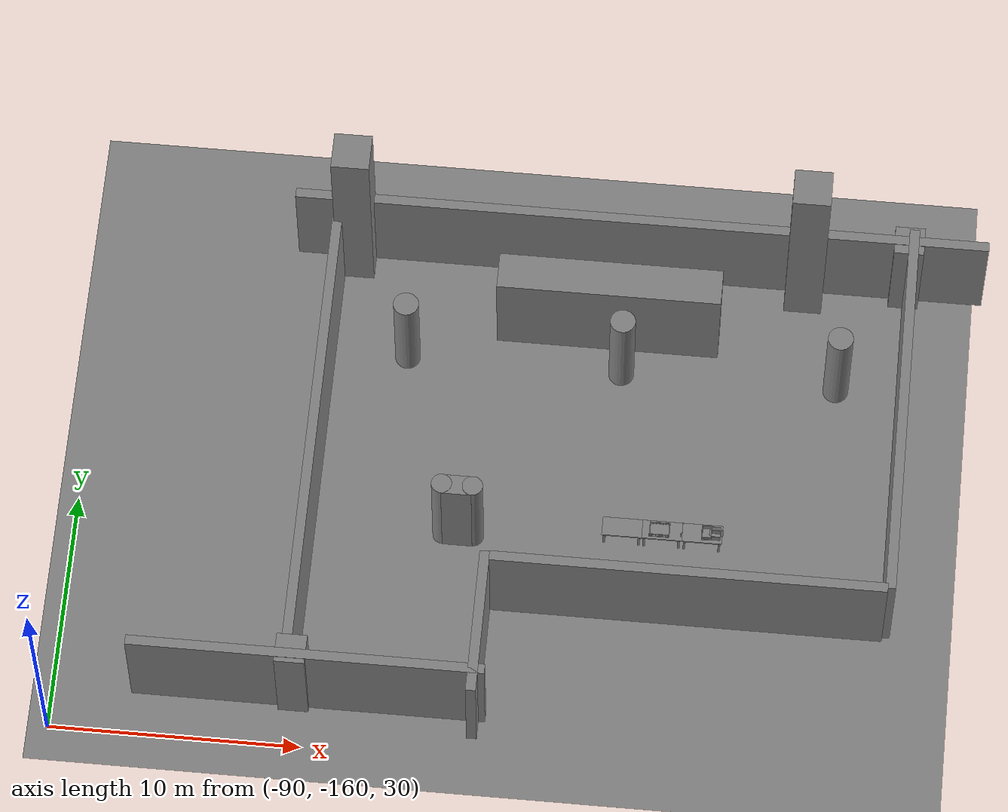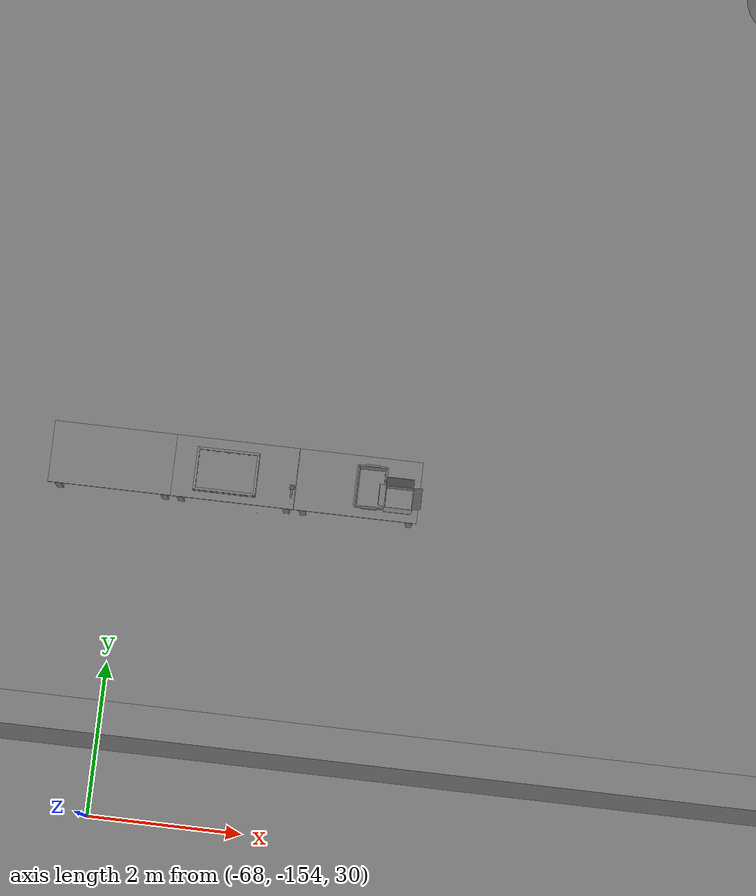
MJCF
<mujoco>
    <option gravity="0.000000000 0.000000000 -9.810000420" timestep="0.0049999999" integrator="implicitfast" density="1.225" viscosity="1.8000001e-05" noslip_iterations="10" iterations="100" sdf_iterations="50">
        <flag multiccd="disable"/>
    </option>
    <size memory="1000M"/>
    <compiler coordinate="local"/>
    <worldbody>
        <light cutoff="30" pos="0 1 1" dir="0 -1 -2"/>
        <light cutoff="30" pos="0 -1 1" dir="0 1 -2"/>
        <body pos="-64.866622925 -149.383972168 30.183746338" euler="89.999992371 89.999946594 0.000000000" name="openloong_gripper_2f85_fix_base_usda_bluebox_01">
            <geom contype="1" conaffinity="1" density="1000" type="box" material="" rgba="0.500000000 0.500000000 0.500000000 1.000000000" solimp="0.899999976 0.949999988 0.001000000" friction="1.000000000 0.005000000 0.000100000" solref="0.020000000 1.000000000" margin="0" condim="3" group="0" pos="0.276596069 0.187225342 0.000061035" quat="0.707107008 0.000077501 0.707106471 0.000077456" size="0.100000001 0.057999998 0.010000000" name="openloong_gripper_2f85_fix_base_usda_geom_D29D8ECA_B8DE_4E63_B6C6_A1BAF2A50CFB"/>
            <geom contype="1" conaffinity="1" density="1000" type="box" material="" rgba="0.500000000 0.500000000 0.500000000 1.000000000" solimp="0.899999976 0.949999988 0.001000000" friction="1.000000000 0.005000000 0.000100000" solref="0.020000000 1.000000000" margin="0" condim="3" group="0" pos="0.000000000 0.002883911 0.000000000" quat="1.000000000 0.000000000 0.000000000 0.000000000" size="0.254000008 0.003000000 0.172000006" name="openloong_gripper_2f85_fix_base_usda_geom_5475DE6B_CF14_41C0_A44D_F490011B82B9"/>
            <geom contype="1" conaffinity="1" density="1000" type="box" material="" rgba="0.500000000 0.500000000 0.500000000 1.000000000" solimp="0.899999976 0.949999988 0.001000000" friction="1.000000000 0.005000000 0.000100000" solref="0.020000000 1.000000000" margin="0" condim="3" group="0" pos="0.000015259 0.124874115 0.173477173" quat="0.999796450 0.020176515 -0.000000015 0.000000030" size="0.259999990 0.119999997 0.007000000" name="openloong_gripper_2f85_fix_base_usda_geom_72DACE54_8680_47BA_920C_DB01F02F7B19"/>
            <geom contype="1" conaffinity="1" density="1000" type="box" material="" rgba="0.500000000 0.500000000 0.500000000 1.000000000" solimp="0.899999976 0.949999988 0.001000000" friction="1.000000000 0.005000000 0.000100000" solref="0.020000000 1.000000000" margin="0" condim="3" group="0" pos="0.000015259 0.124874115 -0.173477173" quat="0.999796450 -0.020176545 -0.000000015 0.000000000" size="0.259999990 0.119999997 0.007000000" name="openloong_gripper_2f85_fix_base_usda_geom_BFE7227F_A006_4963_B358_4F4E9E9571C2"/>
            <geom contype="1" conaffinity="1" density="1000" type="box" material="" rgba="0.500000000 0.500000000 0.500000000 1.000000000" solimp="0.899999976 0.949999988 0.001000000" friction="1.000000000 0.005000000 0.000100000" solref="0.020000000 1.000000000" margin="0" condim="3" group="0" pos="0.000015259 0.214012146 0.188980103" quat="0.999913096 0.013176724 0.000000015 0.000000000" size="0.259999990 0.029999999 0.012500000" name="openloong_gripper_2f85_fix_base_usda_geom_5CD909BF_957D_4BF4_A552_7CDBDA544968"/>
            <geom contype="1" conaffinity="1" density="1000" type="box" material="" rgba="0.500000000 0.500000000 0.500000000 1.000000000" solimp="0.899999976 0.949999988 0.001000000" friction="1.000000000 0.005000000 0.000100000" solref="0.020000000 1.000000000" margin="0" condim="3" group="0" pos="-0.258346558 0.125289917 0.001876831" quat="0.702796996 -0.020792052 0.710783184 0.020769238" size="0.189999998 0.119999997 0.009000000" name="openloong_gripper_2f85_fix_base_usda_geom_8F630B36_1EBC_4825_AA24_6DD633A2EC25"/>
            <geom contype="1" conaffinity="1" density="1000" type="box" material="" rgba="0.500000000 0.500000000 0.500000000 1.000000000" solimp="0.899999976 0.949999988 0.001000000" friction="1.000000000 0.005000000 0.000100000" solref="0.020000000 1.000000000" margin="0" condim="3" group="0" pos="0.000015259 0.214012146 -0.188980103" quat="0.999913096 -0.013176769 0.000000030 0.000000015" size="0.259999990 0.029999999 0.012500000" name="openloong_gripper_2f85_fix_base_usda_geom_81DBC7C8_9AA7_404D_AFC6_F660A424A752"/>
            <geom contype="1" conaffinity="1" density="1000" type="box" material="" rgba="0.500000000 0.500000000 0.500000000 1.000000000" solimp="0.899999976 0.949999988 0.001000000" friction="1.000000000 0.005000000 0.000100000" solref="0.020000000 1.000000000" margin="0" condim="3" group="0" pos="-0.276596069 0.187225342 0.000061035" quat="0.707106650 0.000077441 0.707106709 0.000077456" size="0.100000001 0.057999998 0.010000000" name="openloong_gripper_2f85_fix_base_usda_geom_E4723BDD_B7E3_4FB1_B693_621C517784E8"/>
            <geom contype="1" conaffinity="1" density="1000" type="box" material="" rgba="0.500000000 0.500000000 0.500000000 1.000000000" solimp="0.899999976 0.949999988 0.001000000" friction="1.000000000 0.005000000 0.000100000" solref="0.020000000 1.000000000" margin="0" condim="3" group="0" pos="0.258346558 0.125289917 0.001876831" quat="0.702851534 0.018856451 0.710823834 -0.019329429" size="0.189999998 0.119999997 0.009000000" name="openloong_gripper_2f85_fix_base_usda_geom_88A93A04_8EA7_43A7_A9FA_4DB9ECFB7732"/>
            <freejoint name="openloong_gripper_2f85_fix_base_usda_bluebox_01_joint"/>
            <site size="0.005000000 0.005000000 0.005000000" rgba="0.500000000 0.500000000 0.500000000 1.000000000" pos="0.000000000 0.000000000 0.000000000" quat="0.999961913 0.008726534 0.000000000 0.000000000" group="0" type="sphere" name="openloong_gripper_2f85_fix_base_usda_bluebox_01site"/>
        </body>
        <body pos="-64.496299744 -149.491867065 30.235729218" euler="0.000000000 0.000000000 89.999946594" name="openloong_gripper_2f85_fix_base_usda_cardboardbox_01">
            <geom contype="1" conaffinity="1" density="1000" type="box" material="" rgba="0.500000000 0.500000000 0.500000000 1.000000000" solimp="0.899999976 0.949999988 0.001000000" friction="1.000000000 0.005000000 0.000100000" solref="0.020000000 1.000000000" margin="0" condim="3" group="0" pos="-0.003166199 -0.004086494 0.005052090" quat="1.000000000 0.000000000 0.000000000 0.000000000" size="0.142499998 0.177500010 0.005000000" name="openloong_gripper_2f85_fix_base_usda_geom_468998A8_7485_4D10_9206_21602EC65931"/>
            <geom contype="1" conaffinity="1" density="1000" type="box" material="" rgba="0.500000000 0.500000000 0.500000000 1.000000000" solimp="0.899999976 0.949999988 0.001000000" friction="1.000000000 0.005000000 0.000100000" solref="0.020000000 1.000000000" margin="0" condim="3" group="0" pos="-0.003166199 0.170316696 0.150570869" quat="1.000000000 0.000000000 0.000000000 0.000000000" size="0.142499998 0.005000000 0.149999991" name="openloong_gripper_2f85_fix_base_usda_geom_477D0825_0723_459E_BBF3_2492AF6B4460"/>
            <geom contype="1" conaffinity="1" density="1000" type="box" material="" rgba="0.500000000 0.500000000 0.500000000 1.000000000" solimp="0.899999976 0.949999988 0.001000000" friction="1.000000000 0.005000000 0.000100000" solref="0.020000000 1.000000000" margin="0" condim="3" group="0" pos="-0.147399902 -0.005307198 0.150570869" quat="1.000000000 0.000000000 0.000000000 0.000000000" size="0.005000000 0.177500010 0.149999991" name="openloong_gripper_2f85_fix_base_usda_geom_A7B12746_4897_4F4A_A044_690BF1AD8603"/>
            <geom contype="1" conaffinity="1" density="1000" type="box" material="" rgba="0.500000000 0.500000000 0.500000000 1.000000000" solimp="0.899999976 0.949999988 0.001000000" friction="1.000000000 0.005000000 0.000100000" solref="0.020000000 1.000000000" margin="0" condim="3" group="0" pos="0.140275955 -0.005307198 0.150570869" quat="1.000000000 0.000000000 0.000000000 0.000000000" size="0.005000000 0.177500010 0.149999991" name="openloong_gripper_2f85_fix_base_usda_geom_1B80FF7B_9388_4E05_B2F8_93EAC20D36FD"/>
            <geom contype="1" conaffinity="1" density="1000" type="box" material="" rgba="0.500000000 0.500000000 0.500000000 1.000000000" solimp="0.899999976 0.949999988 0.001000000" friction="1.000000000 0.005000000 0.000100000" solref="0.020000000 1.000000000" margin="0" condim="3" group="0" pos="-0.003166199 -0.181550980 0.150570869" quat="1.000000000 0.000000000 0.000000000 0.000000000" size="0.142499998 0.005000000 0.149999991" name="openloong_gripper_2f85_fix_base_usda_geom_11C8C64D_EF72_4C21_8367_2E3B5E559831"/>
            <freejoint name="openloong_gripper_2f85_fix_base_usda_cardboardbox_01_joint"/>
            <site size="0.005000000 0.005000000 0.005000000" rgba="0.500000000 0.500000000 0.500000000 1.000000000" pos="0.000000000 0.000000000 0.000000000" quat="0.999961913 0.008726535 0.000000000 0.000000000" group="0" type="sphere" name="openloong_gripper_2f85_fix_base_usda_site_04390438_0924_4051_A24D_48956BB89BC2"/>
            <body pos="0.139160156 -0.004048347 0.301930904" euler="-179.999954224 49.383502960 179.999954224" name="openloong_gripper_2f85_fix_base_usda_A1_006">
                <geom contype="1" conaffinity="1" density="1000" type="box" material="" rgba="0.500000000 0.500000000 0.500000000 1.000000000" solimp="0.899999976 0.949999988 0.001000000" friction="1.000000000 0.005000000 0.000100000" solref="0.020000000 1.000000000" margin="0" condim="3" group="0" pos="-0.071587563 0.000009537 0.001745224" quat="0.999999881 0.000000000 0.000000000 0.000000000" size="0.071249999 0.179999992 0.002500000" name="openloong_gripper_2f85_fix_base_usda_geom_4723B622_BB4C_45D3_BB34_894D5FAF10E1"/>
                <joint armature="0" stiffness="0.07" damping="0.0099999998" axis="0.000000 1.000000 0.000000" type="hinge" name="openloong_gripper_2f85_fix_base_usda_A1_006"/>
            </body>
            <body pos="-0.145902634 -0.004086494 0.301938057" euler="-180.000000000 -60.000011444 -180.000000000" name="openloong_gripper_2f85_fix_base_usda_A2_006">
                <geom contype="1" conaffinity="1" density="1000" type="box" material="" rgba="0.500000000 0.500000000 0.500000000 1.000000000" solimp="0.899999976 0.949999988 0.001000000" friction="1.000000000 0.005000000 0.000100000" solref="0.020000000 1.000000000" margin="0" condim="3" group="0" pos="0.071268082 0.000009537 0.002717972" quat="0.000002921 0.000000000 -0.000000030 0.999999881" size="0.071249999 0.179999992 0.002500000" name="openloong_gripper_2f85_fix_base_usda_geom_860CCC8E_C061_44DA_89F3_0797B874F574"/>
                <joint armature="0" stiffness="0.07" damping="0.0099999998" axis="0.000000 1.000000 0.000000" type="hinge" name="openloong_gripper_2f85_fix_base_usda_A2_006"/>
            </body>
            <body pos="-0.003385544 0.175991058 0.301930904" euler="-125.858116150 -0.000004561 0.000002331" name="openloong_gripper_2f85_fix_base_usda_B2_006">
                <geom contype="1" conaffinity="1" density="1000" type="box" material="" rgba="0.500000000 0.500000000 0.500000000 1.000000000" solimp="0.899999976 0.949999988 0.001000000" friction="1.000000000 0.005000000 0.000100000" solref="0.020000000 1.000000000" margin="0" condim="3" group="0" pos="0.000009537 -0.070939064 -0.002470016" quat="0.999614120 0.027776197 -0.000000015 0.000000030" size="0.137500003 0.064999998 0.005000000" name="openloong_gripper_2f85_fix_base_usda_geom_F98AE07F_01EE_407A_A0E1_756DB6AA150F"/>
                <joint armature="0" stiffness="0.07" damping="0.0099999998" axis="1.000000 0.000000 0.000000" type="hinge" name="openloong_gripper_2f85_fix_base_usda_B2_006"/>
            </body>
            <body pos="-0.003385544 -0.184140205 0.301938057" euler="147.805557251 0.000000000 0.000000000" name="openloong_gripper_2f85_fix_base_usda_B1_006">
                <geom contype="1" conaffinity="1" density="1000" type="box" material="" rgba="0.500000000 0.500000000 0.500000000 1.000000000" solimp="0.899999976 0.949999988 0.001000000" friction="1.000000000 0.005000000 0.000100000" solref="0.020000000 1.000000000" margin="0" condim="3" group="0" pos="-0.000028610 0.070202351 -0.002703667" quat="0.999614179 -0.027776167 0.000000000 0.000000000" size="0.137500003 0.064999998 0.005000000" name="openloong_gripper_2f85_fix_base_usda_geom_37D51E2B_64DD_4D08_8C5B_36985F6B14AC"/>
                <joint armature="0" stiffness="0.07" damping="0.0099999998" axis="1.000000 0.000000 0.000000" type="hinge" name="openloong_gripper_2f85_fix_base_usda_B1_006"/>
            </body>
        </body>
        <body pos="-65.882858276 -149.481979370 30.229999542" euler="-64.487716675 0.000000000 0.000000000" name="openloong_gripper_2f85_fix_base_usda_Barcode">
            <geom contype="1" conaffinity="1" density="1000" type="box" material="" rgba="0.500000000 0.500000000 0.500000000 1.000000000" solimp="0.899999976 0.949999988 0.001000000" friction="1.000000000 0.005000000 0.000100000" solref="0.020000000 1.000000000" margin="0" condim="3" group="0" pos="0.000000000 0.013038635 0.001419067" quat="0.000000000 0.000000000 0.000000000 1.000000119" size="0.034000002 0.010000000 0.017999999" name="openloong_gripper_2f85_fix_base_usda_geom_FCB755A1_4369_4EB7_9A0B_7551C1A12519"/>
            <geom contype="1" conaffinity="1" density="1000" type="box" material="" rgba="0.500000000 0.500000000 0.500000000 1.000000000" solimp="0.899999976 0.949999988 0.001000000" friction="1.000000000 0.005000000 0.000100000" solref="0.020000000 1.000000000" margin="0" condim="3" group="0" pos="0.000000000 -0.035301208 -0.007095337" quat="0.000000000 0.000000000 -0.043619365 0.999048233" size="0.028999999 0.010000000 0.020000000" name="openloong_gripper_2f85_fix_base_usda_geom_214624C4_0AFD_4544_A679_8AC97920FE29"/>
            <geom contype="1" conaffinity="1" density="1000" type="box" material="" rgba="0.500000000 0.500000000 0.500000000 1.000000000" solimp="0.899999976 0.949999988 0.001000000" friction="1.000000000 0.005000000 0.000100000" solref="0.020000000 1.000000000" margin="0" condim="3" group="0" pos="0.000000000 -0.043411255 -0.011749268" quat="0.922262907 0.386563420 0.000000000 0.000000000" size="0.026000001 0.010000000 0.020000000" name="openloong_gripper_2f85_fix_base_usda_geom_9105EEA4_4458_4604_9F09_E2EF87916414"/>
            <geom contype="1" conaffinity="1" density="1000" type="box" material="" rgba="0.500000000 0.500000000 0.500000000 1.000000000" solimp="0.899999976 0.949999988 0.001000000" friction="1.000000000 0.005000000 0.000100000" solref="0.020000000 1.000000000" margin="0" condim="3" group="0" pos="0.000000000 -0.016967773 -0.031860352" quat="0.000000000 0.000000000 0.000000000 1.000000119" size="0.008000000 0.010000000 0.013000000" name="openloong_gripper_2f85_fix_base_usda_geom_1E393299_378D_423C_BEA0_0BB8B8165B7F"/>
            <geom contype="1" conaffinity="1" density="1000" type="box" material="" rgba="0.500000000 0.500000000 0.500000000 1.000000000" solimp="0.899999976 0.949999988 0.001000000" friction="1.000000000 0.005000000 0.000100000" solref="0.020000000 1.000000000" margin="0" condim="3" group="0" pos="0.000000000 -0.001869202 0.000312805" quat="0.953716993 0.300705761 0.000000000 0.000000000" size="0.032000002 0.010000000 0.018999999" name="openloong_gripper_2f85_fix_base_usda_geom_1CEA8694_8161_41A3_86D7_59FB9B441C10"/>
            <geom contype="1" conaffinity="1" density="1000" type="box" material="" rgba="0.500000000 0.500000000 0.500000000 1.000000000" solimp="0.899999976 0.949999988 0.001000000" friction="1.000000000 0.005000000 0.000100000" solref="0.020000000 1.000000000" margin="0" condim="3" group="0" pos="0.000000000 -0.019531250 -0.003173828" quat="0.953716993 0.300705761 0.000000000 0.000000000" size="0.030999999 0.010000000 0.020000000" name="openloong_gripper_2f85_fix_base_usda_geom_D71C3CB5_36B3_4C02_9494_7F12A55F44E0"/>
            <geom contype="1" conaffinity="1" density="1000" type="box" material="" rgba="0.500000000 0.500000000 0.500000000 1.000000000" solimp="0.899999976 0.949999988 0.001000000" friction="1.000000000 0.005000000 0.000100000" solref="0.020000000 1.000000000" margin="0" condim="3" group="0" pos="0.000000000 -0.035301208 -0.007095337" quat="0.953716993 0.300705761 0.000000000 0.000000000" size="0.028999999 0.010000000 0.020000000" name="openloong_gripper_2f85_fix_base_usda_geom_EE987B63_4E2D_4533_A3F4_2754CFC91D92"/>
            <geom contype="1" conaffinity="1" density="1000" type="box" material="" rgba="0.500000000 0.500000000 0.500000000 1.000000000" solimp="0.899999976 0.949999988 0.001000000" friction="1.000000000 0.005000000 0.000100000" solref="0.020000000 1.000000000" margin="0" condim="3" group="0" pos="0.000000000 -0.042617798 -0.071121216" quat="0.000000000 0.000000000 0.000000000 1.000000119" size="0.013000000 0.021000000 0.059999999" name="openloong_gripper_2f85_fix_base_usda_geom_0ECC0E98_7B88_4E37_BEC1_8E89FF82D338"/>
            <freejoint name="openloong_gripper_2f85_fix_base_usda_Barcode_joint"/>
            <site size="0.005000000 0.005000000 0.005000000" rgba="0.500000000 0.500000000 0.500000000 1.000000000" pos="0.000000000 0.000000000 0.000000000" quat="1.000000000 0.000000000 0.000000000 0.000000000" group="0" type="sphere" name="openloong_gripper_2f85_fix_base_usda_Barcode_site"/>
        </body>
        <body pos="-66.745018005 -149.392349243 30.184000015" euler="0.000000000 0.000000000 89.999946594" name="[22332418687237]_Basket_01">
            <geom contype="1" conaffinity="1" density="1000" type="box" material="" rgba="0.500000000 0.500000000 0.500000000 1.000000000" solimp="0.899999976 0.949999988 0.001000000" friction="1.000000000 0.005000000 0.000100000" solref="0.020000000 1.000000000" margin="0" condim="3" group="0" pos="-0.052425385 0.389207840 0.089787483" quat="0.707107008 0.000000000 0.000000000 0.707106411" size="0.014249999 0.014249999 0.059999999" name="[22332418687237]_geom_79BE2071_0A44_401C_B2E0_703A35C7988D"/>
            <geom contype="1" conaffinity="1" density="1000" type="box" material="" rgba="0.500000000 0.500000000 0.500000000 1.000000000" solimp="0.899999976 0.949999988 0.001000000" friction="1.000000000 0.005000000 0.000100000" solref="0.020000000 1.000000000" margin="0" condim="3" group="0" pos="0.264015198 -0.133043289 0.089787483" quat="0.707107008 0.000000000 0.000000000 0.707106411" size="0.014249999 0.014249999 0.059999999" name="[22332418687237]_geom_D8D0EDE2_320B_4AF8_96BA_1E5C86074B7E"/>
            <geom contype="1" conaffinity="1" density="1000" type="box" material="" rgba="0.500000000 0.500000000 0.500000000 1.000000000" solimp="0.899999976 0.949999988 0.001000000" friction="1.000000000 0.005000000 0.000100000" solref="0.020000000 1.000000000" margin="0" condim="3" group="0" pos="-0.264015198 -0.265548706 0.089793205" quat="0.707107008 0.000000000 0.000000000 0.707106411" size="0.014249999 0.014249999 0.059999999" name="[22332418687237]_geom_0DAEF97B_1B35_4FB3_9F53_20B7237F944E"/>
            <geom contype="1" conaffinity="1" density="1000" type="box" material="" rgba="0.500000000 0.500000000 0.500000000 1.000000000" solimp="0.899999976 0.949999988 0.001000000" friction="1.000000000 0.005000000 0.000100000" solref="0.020000000 1.000000000" margin="0" condim="3" group="0" pos="-0.160263062 -0.389322281 0.089793205" quat="0.707107008 0.000000000 0.000000000 0.707106411" size="0.014249999 0.014249999 0.059999999" name="[22332418687237]_geom_7CB54E7C_0FCC_41BD_A17A_5C9354348477"/>
            <geom contype="1" conaffinity="1" density="1000" type="box" material="" rgba="0.500000000 0.500000000 0.500000000 1.000000000" solimp="0.899999976 0.949999988 0.001000000" friction="1.000000000 0.005000000 0.000100000" solref="0.020000000 1.000000000" margin="0" condim="3" group="0" pos="0.162265778 -0.389322281 0.089787483" quat="0.707107008 0.000000000 0.000000000 0.707106411" size="0.014249999 0.014249999 0.059999999" name="[22332418687237]_geom_6AD24B1D_FF58_43D6_844A_225097AEBB16"/>
            <geom contype="1" conaffinity="1" density="1000" type="box" material="" rgba="0.500000000 0.500000000 0.500000000 1.000000000" solimp="0.899999976 0.949999988 0.001000000" friction="1.000000000 0.005000000 0.000100000" solref="0.020000000 1.000000000" margin="0" condim="3" group="0" pos="0.264015198 0.389207840 0.089787483" quat="0.707107008 0.000000000 0.000000000 0.707106411" size="0.014249999 0.014249999 0.059999999" name="[22332418687237]_geom_D0FB4386_5B55_4C14_9643_760C4706237C"/>
            <geom contype="1" conaffinity="1" density="1000" type="box" material="" rgba="0.500000000 0.500000000 0.500000000 1.000000000" solimp="0.899999976 0.949999988 0.001000000" friction="1.000000000 0.005000000 0.000100000" solref="0.020000000 1.000000000" margin="0" condim="3" group="0" pos="-0.264015198 -0.133043289 0.089793205" quat="0.707107008 0.000000000 0.000000000 0.707106411" size="0.014249999 0.014249999 0.059999999" name="[22332418687237]_geom_BEC05AF2_D6FD_49E5_B6DE_5F8D64A9342A"/>
            <geom contype="1" conaffinity="1" density="1000" type="box" material="" rgba="0.500000000 0.500000000 0.500000000 1.000000000" solimp="0.899999976 0.949999988 0.001000000" friction="1.000000000 0.005000000 0.000100000" solref="0.020000000 1.000000000" margin="0" condim="3" group="0" pos="-0.264026642 0.269256592 0.089793205" quat="0.707107008 0.000000000 0.000000000 0.707106411" size="0.014249999 0.014249999 0.059999999" name="[22332418687237]_geom_0A10BF8C_5D62_4F30_A9B2_CB44B8ACDC85"/>
            <geom contype="1" conaffinity="1" density="1000" type="box" material="" rgba="0.500000000 0.500000000 0.500000000 1.000000000" solimp="0.899999976 0.949999988 0.001000000" friction="1.000000000 0.005000000 0.000100000" solref="0.020000000 1.000000000" margin="0" condim="3" group="0" pos="0.054462433 0.389207840 0.089787483" quat="0.707107008 0.000000000 0.000000000 0.707106411" size="0.014249999 0.014249999 0.059999999" name="[22332418687237]_geom_9A0D3D98_36B5_4E22_B2B1_1A128194EF2E"/>
            <geom contype="1" conaffinity="1" density="1000" type="box" material="" rgba="0.500000000 0.500000000 0.500000000 1.000000000" solimp="0.899999976 0.949999988 0.001000000" friction="1.000000000 0.005000000 0.000100000" solref="0.020000000 1.000000000" margin="0" condim="3" group="0" pos="0.054462433 -0.389322281 0.089787483" quat="0.707107008 0.000000000 0.000000000 0.707106411" size="0.014249999 0.014249999 0.059999999" name="[22332418687237]_geom_B868AAB6_A8F5_4C51_8CD6_B6468D5BB3C7"/>
            <geom contype="1" conaffinity="1" density="1000" type="box" material="" rgba="0.500000000 0.500000000 0.500000000 1.000000000" solimp="0.899999976 0.949999988 0.001000000" friction="1.000000000 0.005000000 0.000100000" solref="0.020000000 1.000000000" margin="0" condim="3" group="0" pos="0.264015198 0.269256592 0.089793205" quat="0.707107008 0.000000000 0.000000000 0.707106411" size="0.014249999 0.014249999 0.059999999" name="[22332418687237]_geom_01E7B2DA_04CB_41AE_9F21_A7C1DBD5E927"/>
            <geom contype="1" conaffinity="1" density="1000" type="box" material="" rgba="0.500000000 0.500000000 0.500000000 1.000000000" solimp="0.899999976 0.949999988 0.001000000" friction="1.000000000 0.005000000 0.000100000" solref="0.020000000 1.000000000" margin="0" condim="3" group="0" pos="0.264015198 -0.389322281 0.089787483" quat="0.707107008 0.000000000 0.000000000 0.707106411" size="0.014249999 0.014249999 0.059999999" name="[22332418687237]_geom_14C3FF27_1762_40F7_A2C3_A26FDC978159"/>
            <geom contype="1" conaffinity="1" density="1000" type="box" material="" rgba="0.500000000 0.500000000 0.500000000 1.000000000" solimp="0.899999976 0.949999988 0.001000000" friction="1.000000000 0.005000000 0.000100000" solref="0.020000000 1.000000000" margin="0" condim="3" group="0" pos="0.000000000 0.000000000 0.015998840" quat="0.707107008 0.000000000 0.000000000 0.707106411" size="0.403499991 0.279000014 0.015750000" name="[22332418687237]_geom_BEF9D75B_141A_466C_AB14_AF036AD1C78B"/>
            <geom contype="1" conaffinity="1" density="1000" type="box" material="" rgba="0.500000000 0.500000000 0.500000000 1.000000000" solimp="0.899999976 0.949999988 0.001000000" friction="1.000000000 0.005000000 0.000100000" solref="0.020000000 1.000000000" margin="0" condim="3" group="0" pos="0.000000000 -0.389476776 0.163619041" quat="0.707107008 0.000000000 0.000000000 0.707106411" size="0.015000000 0.277500004 0.015750000" name="[22332418687237]_geom_077DB44F_53E0_4F70_9992_80A4B061ECBB"/>
            <geom contype="1" conaffinity="1" density="1000" type="box" material="" rgba="0.500000000 0.500000000 0.500000000 1.000000000" solimp="0.899999976 0.949999988 0.001000000" friction="1.000000000 0.005000000 0.000100000" solref="0.020000000 1.000000000" margin="0" condim="3" group="0" pos="0.162265778 0.389207840 0.089787483" quat="0.707107008 0.000000000 0.000000000 0.707106411" size="0.014249999 0.014249999 0.059999999" name="[22332418687237]_geom_07903523_F371_4E76_8BDB_FC98686C6413"/>
            <geom contype="1" conaffinity="1" density="1000" type="box" material="" rgba="0.500000000 0.500000000 0.500000000 1.000000000" solimp="0.899999976 0.949999988 0.001000000" friction="1.000000000 0.005000000 0.000100000" solref="0.020000000 1.000000000" margin="0" condim="3" group="0" pos="0.000000000 0.389471054 0.163619041" quat="0.707107008 0.000000000 0.000000000 0.707106411" size="0.015000000 0.277500004 0.015750000" name="[22332418687237]_geom_413F8F5E_0AE9_433C_B9FB_13CFD6E8EB15"/>
            <geom contype="1" conaffinity="1" density="1000" type="box" material="" rgba="0.500000000 0.500000000 0.500000000 1.000000000" solimp="0.899999976 0.949999988 0.001000000" friction="1.000000000 0.005000000 0.000100000" solref="0.020000000 1.000000000" margin="0" condim="3" group="0" pos="-0.263511658 0.000000000 0.163619041" quat="0.707107008 0.000000000 0.000000000 0.707106411" size="0.403499991 0.015000000 0.015750000" name="[22332418687237]_geom_C7EA1254_3AA3_4ADE_A7C6_E66CB412338F"/>
            <geom contype="1" conaffinity="1" density="1000" type="box" material="" rgba="0.500000000 0.500000000 0.500000000 1.000000000" solimp="0.899999976 0.949999988 0.001000000" friction="1.000000000 0.005000000 0.000100000" solref="0.020000000 1.000000000" margin="0" condim="3" group="0" pos="-0.264015198 0.141334534 0.089793205" quat="0.707107008 0.000000000 0.000000000 0.707106411" size="0.014249999 0.014249999 0.059999999" name="[22332418687237]_geom_9E766917_F6E6_4508_BE72_DC49E2511AE1"/>
            <geom contype="1" conaffinity="1" density="1000" type="box" material="" rgba="0.500000000 0.500000000 0.500000000 1.000000000" solimp="0.899999976 0.949999988 0.001000000" friction="1.000000000 0.005000000 0.000100000" solref="0.020000000 1.000000000" margin="0" condim="3" group="0" pos="0.264015198 -0.265548706 0.089787483" quat="0.707107008 0.000000000 0.000000000 0.707106411" size="0.014249999 0.014249999 0.059999999" name="[22332418687237]_geom_7061B69A_EA1E_4AD6_AB12_B1FC22CCD422"/>
            <geom contype="1" conaffinity="1" density="1000" type="box" material="" rgba="0.500000000 0.500000000 0.500000000 1.000000000" solimp="0.899999976 0.949999988 0.001000000" friction="1.000000000 0.005000000 0.000100000" solref="0.020000000 1.000000000" margin="0" condim="3" group="0" pos="-0.160263062 0.389207840 0.089787483" quat="0.707107008 0.000000000 0.000000000 0.707106411" size="0.014249999 0.014249999 0.059999999" name="[22332418687237]_geom_90F8D638_272B_47CA_93FF_32C9F16BCF98"/>
            <geom contype="1" conaffinity="1" density="1000" type="box" material="" rgba="0.500000000 0.500000000 0.500000000 1.000000000" solimp="0.899999976 0.949999988 0.001000000" friction="1.000000000 0.005000000 0.000100000" solref="0.020000000 1.000000000" margin="0" condim="3" group="0" pos="-0.052425385 -0.389322281 0.089787483" quat="0.707107008 0.000000000 0.000000000 0.707106411" size="0.014249999 0.014249999 0.059999999" name="[22332418687237]_geom_231E3B79_02BB_48CC_94C8_D84893F95E8B"/>
            <geom contype="1" conaffinity="1" density="1000" type="box" material="" rgba="0.500000000 0.500000000 0.500000000 1.000000000" solimp="0.899999976 0.949999988 0.001000000" friction="1.000000000 0.005000000 0.000100000" solref="0.020000000 1.000000000" margin="0" condim="3" group="0" pos="-0.264026642 -0.389322281 0.089793205" quat="0.707107008 0.000000000 0.000000000 0.707106411" size="0.014249999 0.014249999 0.059999999" name="[22332418687237]_geom_0DD4242D_3F0F_4EAA_8CBB_45A935599BBD"/>
            <geom contype="1" conaffinity="1" density="1000" type="box" material="" rgba="0.500000000 0.500000000 0.500000000 1.000000000" solimp="0.899999976 0.949999988 0.001000000" friction="1.000000000 0.005000000 0.000100000" solref="0.020000000 1.000000000" margin="0" condim="3" group="0" pos="0.264015198 0.141334534 0.089787483" quat="0.707107008 0.000000000 0.000000000 0.707106411" size="0.014249999 0.014249999 0.059999999" name="[22332418687237]_geom_A69BE419_4C62_4E83_AE47_6E317FE67B7E"/>
            <geom contype="1" conaffinity="1" density="1000" type="box" material="" rgba="0.500000000 0.500000000 0.500000000 1.000000000" solimp="0.899999976 0.949999988 0.001000000" friction="1.000000000 0.005000000 0.000100000" solref="0.020000000 1.000000000" margin="0" condim="3" group="0" pos="-0.264015198 0.389207840 0.089793205" quat="0.707107008 0.000000000 0.000000000 0.707106411" size="0.014249999 0.014249999 0.059999999" name="[22332418687237]_geom_D79E4509_CEDD_4B10_9756_0B8DCE83027B"/>
            <geom contype="1" conaffinity="1" density="1000" type="box" material="" rgba="0.500000000 0.500000000 0.500000000 1.000000000" solimp="0.899999976 0.949999988 0.001000000" friction="1.000000000 0.005000000 0.000100000" solref="0.020000000 1.000000000" margin="0" condim="3" group="0" pos="0.264015198 0.004480362 0.089787483" quat="0.707107008 0.000000000 0.000000000 0.707106411" size="0.014249999 0.014249999 0.059999999" name="[22332418687237]_geom_692C0BD2_98DA_4E98_9A2D_50AF749CD522"/>
            <geom contype="1" conaffinity="1" density="1000" type="box" material="" rgba="0.500000000 0.500000000 0.500000000 1.000000000" solimp="0.899999976 0.949999988 0.001000000" friction="1.000000000 0.005000000 0.000100000" solref="0.020000000 1.000000000" margin="0" condim="3" group="0" pos="0.263694763 -0.000011444 0.163619041" quat="0.707107008 0.000000000 0.000000000 0.707106411" size="0.403499991 0.015000000 0.015750000" name="[22332418687237]_geom_5E0FCFD4_66E3_4628_9528_5145800A15EB"/>
            <geom contype="1" conaffinity="1" density="1000" type="box" material="" rgba="0.500000000 0.500000000 0.500000000 1.000000000" solimp="0.899999976 0.949999988 0.001000000" friction="1.000000000 0.005000000 0.000100000" solref="0.020000000 1.000000000" margin="0" condim="3" group="0" pos="-0.264015198 0.004480362 0.089793205" quat="0.707107008 0.000000000 0.000000000 0.707106411" size="0.014249999 0.014249999 0.059999999" name="[22332418687237]_geom_2255CCE3_7E8F_43B7_854F_F317B6B21046"/>
            <freejoint name="[22332418687237]_joint_41ADD061_9B04_440B_BF6E_297CFC9ED5C5"/>
        </body>
        <body pos="0.000000000 0.000000000 0.000000000" euler="0.000000000 0.000000000 0.000000000" name="Static Objects_Static Objects">
            <geom contype="1" conaffinity="1" density="1000" type="box" material="" rgba="0.500000000 0.500000000 0.500000000 1.000000000" solimp="0.899999976 0.949999988 0.001000000" friction="1.000000000 0.005000000 0.000100000" solref="0.020000000 1.000000000" margin="0" condim="3" group="0" pos="-67.544113159 -149.365814209 29.727830887" quat="0.500000417 0.499999970 0.499999553 0.499999970" size="0.381000012 0.319999993 0.041000001" name="Static Objects_geom_7021EDD3_00F5_410E_A9C8_4F35EBFD870C"/>
            <geom contype="1" conaffinity="1" density="1000" type="box" material="" rgba="0.500000000 0.500000000 0.500000000 1.000000000" solimp="0.899999976 0.949999988 0.001000000" friction="1.000000000 0.005000000 0.000100000" solref="0.020000000 1.000000000" margin="0" condim="3" group="0" pos="-68.239501953 -149.365814209 30.086868286" quat="0.500000417 0.499999970 0.499999553 0.499999970" size="0.370999992 0.039500002 0.745000005" name="Static Objects_geom_3BEDAD8F_8047_4F8D_AB20_8D306FF3870D"/>
            <geom contype="1" conaffinity="1" density="1000" type="box" material="" rgba="0.500000000 0.500000000 0.500000000 1.000000000" solimp="0.899999976 0.949999988 0.001000000" friction="1.000000000 0.005000000 0.000100000" solref="0.020000000 1.000000000" margin="0" condim="3" group="0" pos="-68.239501953 -149.365814209 30.147235870" quat="0.500000417 0.499999970 0.499999553 0.499999970" size="0.400000006 0.022000000 0.800000012" name="Static Objects_geom_6AC63D9C_FBFC_44D7_9A9D_BDEEEA78AA2B"/>
            <geom contype="1" conaffinity="1" density="1000" type="box" material="" rgba="0.500000000 0.500000000 0.500000000 1.000000000" solimp="0.899999976 0.949999988 0.001000000" friction="1.000000000 0.005000000 0.000100000" solref="0.020000000 1.000000000" margin="0" condim="3" group="0" pos="-68.934890747 -149.365814209 29.727830887" quat="0.500000417 0.499999970 0.499999553 0.499999970" size="0.381000012 0.319999993 0.041000001" name="Static Objects_geom_B559E2A9_5846_44C3_B3A9_47523C678C1A"/>
            <geom contype="1" conaffinity="1" density="1000" type="box" material="" rgba="0.500000000 0.500000000 0.500000000 1.000000000" solimp="0.899999976 0.949999988 0.001000000" friction="1.000000000 0.005000000 0.000100000" solref="0.020000000 1.000000000" margin="0" condim="3" group="0" pos="-68.239501953 -149.365814209 29.561563492" quat="0.500000417 0.499999970 0.499999553 0.499999970" size="0.020000000 0.022000000 0.660000026" name="Static Objects_geom_E9927398_72B0_4669_B54F_76B4234C2EEC"/>
            <geom contype="1" conaffinity="1" density="1000" type="box" material="" rgba="0.500000000 0.500000000 0.500000000 1.000000000" solimp="0.899999976 0.949999988 0.001000000" friction="1.000000000 0.005000000 0.000100000" solref="0.020000000 1.000000000" margin="0" condim="3" group="0" pos="-65.945671082 -149.365814209 29.727830887" quat="0.500000417 0.499999970 0.499999553 0.499999970" size="0.381000012 0.319999993 0.041000001" name="Static Objects_geom_77710135_8112_4CB7_B80D_50DD74506D6B"/>
            <geom contype="1" conaffinity="1" density="1000" type="box" material="" rgba="0.500000000 0.500000000 0.500000000 1.000000000" solimp="0.899999976 0.949999988 0.001000000" friction="1.000000000 0.005000000 0.000100000" solref="0.020000000 1.000000000" margin="0" condim="3" group="0" pos="-66.641059875 -149.365814209 30.086868286" quat="0.500000417 0.499999970 0.499999553 0.499999970" size="0.370999992 0.039500002 0.745000005" name="Static Objects_geom_76222088_2F43_4688_B164_AF4D897AB469"/>
            <geom contype="1" conaffinity="1" density="1000" type="box" material="" rgba="0.500000000 0.500000000 0.500000000 1.000000000" solimp="0.899999976 0.949999988 0.001000000" friction="1.000000000 0.005000000 0.000100000" solref="0.020000000 1.000000000" margin="0" condim="3" group="0" pos="-66.641059875 -149.365814209 30.147235870" quat="0.500000417 0.499999970 0.499999553 0.499999970" size="0.400000006 0.022000000 0.800000012" name="Static Objects_geom_A008890B_6F3B_47F8_B981_28A0F3F408C2"/>
            <geom contype="1" conaffinity="1" density="1000" type="box" material="" rgba="0.500000000 0.500000000 0.500000000 1.000000000" solimp="0.899999976 0.949999988 0.001000000" friction="1.000000000 0.005000000 0.000100000" solref="0.020000000 1.000000000" margin="0" condim="3" group="0" pos="-67.336448669 -149.365814209 29.727830887" quat="0.500000417 0.499999970 0.499999553 0.499999970" size="0.381000012 0.319999993 0.041000001" name="Static Objects_geom_5CD4E1EF_1440_4E15_9DDA_567929C0D30A"/>
            <geom contype="1" conaffinity="1" density="1000" type="box" material="" rgba="0.500000000 0.500000000 0.500000000 1.000000000" solimp="0.899999976 0.949999988 0.001000000" friction="1.000000000 0.005000000 0.000100000" solref="0.020000000 1.000000000" margin="0" condim="3" group="0" pos="-66.641059875 -149.365814209 29.561563492" quat="0.500000417 0.499999970 0.499999553 0.499999970" size="0.020000000 0.022000000 0.660000026" name="Static Objects_geom_10B45D4F_917D_4631_A05F_BEF2FF8F22FF"/>
            <geom contype="1" conaffinity="1" density="1000" type="box" material="" rgba="0.500000000 0.500000000 0.500000000 1.000000000" solimp="0.899999976 0.949999988 0.001000000" friction="1.000000000 0.005000000 0.000100000" solref="0.020000000 1.000000000" margin="0" condim="3" group="0" pos="-64.338577271 -149.365814209 29.727830887" quat="0.500000417 0.499999970 0.499999553 0.499999970" size="0.381000012 0.319999993 0.041000001" name="Static Objects_geom_76FBEC78_8D96_401D_BC72_7B60CF0CD19B"/>
            <geom contype="1" conaffinity="1" density="1000" type="box" material="" rgba="0.500000000 0.500000000 0.500000000 1.000000000" solimp="0.899999976 0.949999988 0.001000000" friction="1.000000000 0.005000000 0.000100000" solref="0.020000000 1.000000000" margin="0" condim="3" group="0" pos="-65.033966064 -149.365814209 30.086868286" quat="0.500000417 0.499999970 0.499999553 0.499999970" size="0.370999992 0.039500002 0.745000005" name="Static Objects_geom_38A990A4_108D_4936_9BE6_DB9DE37A093B"/>
            <geom contype="1" conaffinity="1" density="1000" type="box" material="" rgba="0.500000000 0.500000000 0.500000000 1.000000000" solimp="0.899999976 0.949999988 0.001000000" friction="1.000000000 0.005000000 0.000100000" solref="0.020000000 1.000000000" margin="0" condim="3" group="0" pos="-65.033966064 -149.365814209 30.147235870" quat="0.500000417 0.499999970 0.499999553 0.499999970" size="0.400000006 0.022000000 0.800000012" name="Static Objects_geom_E11E5310_382D_4872_80E1_1E1EDE058D51"/>
            <geom contype="1" conaffinity="1" density="1000" type="box" material="" rgba="0.500000000 0.500000000 0.500000000 1.000000000" solimp="0.899999976 0.949999988 0.001000000" friction="1.000000000 0.005000000 0.000100000" solref="0.020000000 1.000000000" margin="0" condim="3" group="0" pos="-65.729354858 -149.365814209 29.727830887" quat="0.500000417 0.499999970 0.499999553 0.499999970" size="0.381000012 0.319999993 0.041000001" name="Static Objects_geom_D505CE53_5980_4AC3_B31B_211592748262"/>
            <geom contype="1" conaffinity="1" density="1000" type="box" material="" rgba="0.500000000 0.500000000 0.500000000 1.000000000" solimp="0.899999976 0.949999988 0.001000000" friction="1.000000000 0.005000000 0.000100000" solref="0.020000000 1.000000000" margin="0" condim="3" group="0" pos="-65.033966064 -149.365814209 29.561563492" quat="0.500000417 0.499999970 0.499999553 0.499999970" size="0.020000000 0.022000000 0.660000026" name="Static Objects_geom_E8E523DB_1F0D_484C_BF26_13087F929679"/>
            <geom contype="1" conaffinity="1" density="1000" type="box" material="" rgba="0.500000000 0.500000000 0.500000000 1.000000000" solimp="0.899999976 0.949999988 0.001000000" friction="1.000000000 0.005000000 0.000100000" solref="0.020000000 1.000000000" margin="0" condim="3" group="0" pos="-61.754566193 -137.853729248 33.906845093" quat="0.707107067 0.000000000 0.000000000 0.707106471" size="0.759999990 0.759999990 4.500000000" name="Static Objects_geom_9BACA52F_E856_4962_A387_9829CA7A0B1E"/>
            <geom contype="1" conaffinity="1" density="1000" type="box" material="" rgba="0.500000000 0.500000000 0.500000000 1.000000000" solimp="0.899999976 0.949999988 0.001000000" friction="1.000000000 0.005000000 0.000100000" solref="0.020000000 1.000000000" margin="0" condim="3" group="0" pos="-57.511135101 -144.927108765 31.707921982" quat="1.000000000 0.000000000 0.000000000 0.000000000" size="0.200000003 8.000000000 2.299999952" name="Static Objects_geom_F28A8DBC_00B9_411E_9E3D_9900E7D26058"/>
            <geom contype="1" conaffinity="1" density="1000" type="box" material="" rgba="0.500000000 0.500000000 0.500000000 1.000000000" solimp="0.899999976 0.949999988 0.001000000" friction="1.000000000 0.005000000 0.000100000" solref="0.020000000 1.000000000" margin="0" condim="3" group="0" pos="-80.517646790 -157.574050903 31.688196182" quat="0.707107067 0.000000000 0.000000000 0.707106471" size="0.600000024 0.600000024 2.299999952" name="Static Objects_geom_A6857EF1_F245_4D46_9AEC_55D9F43964DD"/>
            <geom contype="1" conaffinity="1" density="1000" type="box" material="" rgba="0.500000000 0.500000000 0.500000000 1.000000000" solimp="0.899999976 0.949999988 0.001000000" friction="1.000000000 0.005000000 0.000100000" solref="0.020000000 1.000000000" margin="0" condim="3" group="0" pos="-80.711044312 -147.414932251 31.666158676" quat="1.000000000 0.000000000 0.000000000 0.000000000" size="0.200000003 10.000000000 2.299999952" name="Static Objects_geom_B6F24C87_399D_47AF_8F3F_25DC587BF333"/>
            <geom contype="1" conaffinity="1" density="1000" type="box" material="" rgba="0.500000000 0.500000000 0.500000000 1.000000000" solimp="0.899999976 0.949999988 0.001000000" friction="1.000000000 0.005000000 0.000100000" solref="0.020000000 1.000000000" margin="0" condim="3" group="0" pos="-57.687217712 -137.434692383 31.688196182" quat="0.707107067 0.000000000 0.000000000 0.707106471" size="0.600000024 0.600000024 2.299999952" name="Static Objects_geom_A3420346_D661_4F21_A14D_6FA75900DE6C"/>
            <geom contype="1" conaffinity="1" density="1000" type="box" material="" rgba="0.500000000 0.500000000 0.500000000 1.000000000" solimp="0.899999976 0.949999988 0.001000000" friction="1.000000000 0.005000000 0.000100000" solref="0.020000000 1.000000000" margin="0" condim="3" group="0" pos="-69.537033081 -140.263229370 31.714921951" quat="0.707107067 0.000000000 0.000000000 0.707106471" size="0.759999990 4.500000000 2.299999952" name="Static Objects_geom_EDD7E299_2884_49D9_830C_A70FB58ACAB1"/>
            <geom contype="1" conaffinity="1" density="1000" type="box" material="" rgba="0.500000000 0.500000000 0.500000000 1.000000000" solimp="0.899999976 0.949999988 0.001000000" friction="1.000000000 0.005000000 0.000100000" solref="0.020000000 1.000000000" margin="0" condim="3" group="0" pos="-80.073638916 -137.853713989 33.906845093" quat="0.707107067 0.000000000 0.000000000 0.707106471" size="0.759999990 0.759999990 4.500000000" name="Static Objects_geom_62E20495_BB43_4134_B4B3_527AF21E0821"/>
            <geom contype="1" conaffinity="1" density="1000" type="box" material="" rgba="0.500000000 0.500000000 0.500000000 1.000000000" solimp="0.899999976 0.949999988 0.001000000" friction="1.000000000 0.005000000 0.000100000" solref="0.020000000 1.000000000" margin="0" condim="3" group="0" pos="-73.406707764 -155.734664917 31.707921982" quat="1.000000000 0.000000000 0.000000000 0.000000000" size="0.200000003 3.000000000 2.299999952" name="Static Objects_geom_20F68154_2B45_4D8F_BE6A_7BE371331699"/>
            <geom contype="1" conaffinity="1" density="1000" type="box" material="" rgba="0.500000000 0.500000000 0.500000000 1.000000000" solimp="0.899999976 0.949999988 0.001000000" friction="1.000000000 0.005000000 0.000100000" solref="0.020000000 1.000000000" margin="0" condim="3" group="0" pos="-68.497543335 -137.448257446 31.707921982" quat="0.707107067 0.000000000 0.000000000 0.707106471" size="0.200000003 14.000000000 2.299999952" name="Static Objects_geom_EAB90FBE_D56E_459B_B3CE_F626EC25D3C4"/>
            <geom contype="1" conaffinity="1" density="1000" type="cylinder" material="" rgba="0.500000000 0.500000000 0.500000000 1.000000000" solimp="0.899999976 0.949999988 0.001000000" friction="1.000000000 0.005000000 0.000100000" solref="0.020000000 1.000000000" margin="0" condim="3" group="0" pos="-68.868522644 -142.134506226 31.711090088" quat="0.707107067 0.000000000 0.000000000 0.707106471" size="0.509999990 2.299999952 1.000000000" name="Static Objects_geom_D5E83FA4_165B_4F05_82F4_A1663C7BF3ED"/>
            <geom contype="1" conaffinity="1" density="1000" type="plane" material="" rgba="0.500000000 0.500000000 0.500000000 1.000000000" solimp="0.899999976 0.949999988 0.001000000" friction="1.000000000 0.005000000 0.000100000" solref="0.020000000 1.000000000" margin="0" condim="3" group="0" pos="-72.873703003 -147.131927490 29.409669876" quat="1.000000000 0.000000000 0.000000000 0.000000000" size="18.000000000 14.000000000 1.000000000" name="Static Objects_geom_F34A35E7_C3F1_4BC7_B118_EFE4431E7637"/>
            <geom contype="1" conaffinity="1" density="1000" type="box" material="" rgba="0.500000000 0.500000000 0.500000000 1.000000000" solimp="0.899999976 0.949999988 0.001000000" friction="1.000000000 0.005000000 0.000100000" solref="0.020000000 1.000000000" margin="0" condim="3" group="0" pos="-79.943580627 -157.782272339 31.707921982" quat="0.707107067 0.000000000 0.000000000 0.707106471" size="0.200000003 7.000000000 2.299999952" name="Static Objects_geom_E1C9DB0C_1C91_4DBF_B248_9DBDAEA58863"/>
            <geom contype="1" conaffinity="1" density="1000" type="box" material="" rgba="0.500000000 0.500000000 0.500000000 1.000000000" solimp="0.899999976 0.949999988 0.001000000" friction="1.000000000 0.005000000 0.000100000" solref="0.020000000 1.000000000" margin="0" condim="3" group="0" pos="-65.421028137 -152.903442383 31.707921982" quat="0.707107067 0.000000000 0.000000000 0.707106471" size="0.200000003 7.800000191 2.299999952" name="Static Objects_geom_A6BCF252_A170_40AF_8712_B207C28407FB"/>
            <geom contype="1" conaffinity="1" density="1000" type="box" material="" rgba="0.500000000 0.500000000 0.500000000 1.000000000" solimp="0.899999976 0.949999988 0.001000000" friction="1.000000000 0.005000000 0.000100000" solref="0.020000000 1.000000000" margin="0" condim="3" group="0" pos="-74.776908875 -149.964416504 31.688196182" quat="1.000000000 0.000000000 0.000000000 0.000000000" size="0.600000024 0.409999996 2.299999952" name="Static Objects_geom_9DF6F151_35D3_4DE2_8E88_2E01A58B5E6D"/>
            <geom contype="1" conaffinity="1" density="1000" type="cylinder" material="" rgba="0.500000000 0.500000000 0.500000000 1.000000000" solimp="0.899999976 0.949999988 0.001000000" friction="1.000000000 0.005000000 0.000100000" solref="0.020000000 1.000000000" margin="0" condim="3" group="0" pos="-60.161884308 -142.134506226 31.711090088" quat="0.707107067 0.000000000 0.000000000 0.707106471" size="0.509999990 2.299999952 1.000000000" name="Static Objects_geom_08731E3D_7A17_4B79_9F81_3C78B326DCB5"/>
            <geom contype="1" conaffinity="1" density="1000" type="cylinder" material="" rgba="0.500000000 0.500000000 0.500000000 1.000000000" solimp="0.899999976 0.949999988 0.001000000" friction="1.000000000 0.005000000 0.000100000" solref="0.020000000 1.000000000" margin="0" condim="3" group="0" pos="-75.382453918 -149.963455200 31.711090088" quat="0.707107067 0.000000000 0.000000000 0.707106471" size="0.409999996 2.299999952 1.000000000" name="Static Objects_geom_C43E5EC4_5A2E_4CA8_B1EB_E2DB04641D9A"/>
            <geom contype="1" conaffinity="1" density="1000" type="cylinder" material="" rgba="0.500000000 0.500000000 0.500000000 1.000000000" solimp="0.899999976 0.949999988 0.001000000" friction="1.000000000 0.005000000 0.000100000" solref="0.020000000 1.000000000" margin="0" condim="3" group="0" pos="-74.154960632 -149.963455200 31.711090088" quat="0.707107067 0.000000000 0.000000000 0.707106471" size="0.409999996 2.299999952 1.000000000" name="Static Objects_geom_54D687A6_B950_4B03_B2B0_6E975A754846"/>
            <geom contype="1" conaffinity="1" density="1000" type="cylinder" material="" rgba="0.500000000 0.500000000 0.500000000 1.000000000" solimp="0.899999976 0.949999988 0.001000000" friction="1.000000000 0.005000000 0.000100000" solref="0.020000000 1.000000000" margin="0" condim="3" group="0" pos="-77.566612244 -142.134506226 31.711090088" quat="0.707107067 0.000000000 0.000000000 0.707106471" size="0.509999990 2.299999952 1.000000000" name="Static Objects_geom_B942BEFB_BC3D_435A_8DA2_EA2450BB1FF4"/>
        </body>
        <body pos="-66.291030884 -149.869689941 29.018842697" euler="0.000000000 0.000000000 89.999946594" mocap="true" name="openloong_gripper_2f85_fix_base_usda_leftHandMocap"/>
        <body pos="-66.291030884 -149.869689941 29.018842697" euler="0.000000000 0.000000000 89.999946594" mocap="true" name="openloong_gripper_2f85_fix_base_usda_rightHandMocap"/>
        <body pos="-66.291030884 -149.869689941 30.218843460" euler="0.000000000 0.000000000 89.999946594" name="openloong_gripper_2f85_fix_base_usda_base_link">
            <geom contype="1" conaffinity="1" density="1000" type="mesh" material="" rgba="0.783999979 0.783999979 0.783999979 1.000000000" solimp="0.899999976 0.949999988 0.001000000" friction="1.000000000 0.005000000 0.000100000" solref="0.020000000 1.000000000" margin="0" condim="3" group="3" mesh="base_link" pos="0.000000000 0.000000000 0.000000000" quat="1.000000000 0.000000000 0.000000000 0.000000000" size="1.000000000 1.000000000 1.000000000" name="openloong_gripper_2f85_fix_base_usda__geom_7_67C91C48_7A92_41F9_8DAD_762E5FEF552E"/>
            <site size="0.005000000 0.005000000 0.005000000" rgba="0.500000000 0.500000000 0.500000000 1.000000000" pos="0.000000000 0.000000000 0.000000000" quat="1.000000000 0.000000000 0.000000000 0.000000000" group="0" type="sphere" name="openloong_gripper_2f85_fix_base_usda_imu"/>
            <inertial mass="22.447001" pos="-0.005664100 -0.001336700 0.238289997" diaginertia="0.374352545 0.277180195 0.220617250" quat="0.999247074 0.035235517 -0.015086859 0.006023135"/>
            <body pos="0.000000000 0.000000000 0.299997330" euler="0.000000000 0.000000000 0.000000000" name="openloong_gripper_2f85_fix_base_usda_dummy_body">
                <geom contype="1" conaffinity="1" density="1000" type="sphere" material="" rgba="0.783999979 0.783999979 0.783999979 1.000000000" solimp="0.899999976 0.949999988 0.001000000" friction="1.000000000 0.005000000 0.000100000" solref="0.020000000 1.000000000" margin="0" condim="3" group="3" pos="0.000000000 0.000000000 0.000000000" quat="1.000000000 0.000000000 0.000000000 0.000000000" size="0.010000000 0.000000000 0.000000000" name="openloong_gripper_2f85_fix_base_usda__geom_8_420541BF_925C_4AFD_A135_264375AEF0D5"/>
                <joint armature="0.0099999998" stiffness="0" damping="0.1" axis="0.000000 0.000000 1.000000" type="hinge" name="openloong_gripper_2f85_fix_base_usda_dummy_joint"/>
                <site size="0.010000000 0.005000000 0.005000000" rgba="0.500000000 0.500000000 0.500000000 1.000000000" pos="0.000000000 0.000000000 0.000000000" quat="1.000000000 0.000000000 0.000000000 0.000000000" group="3" type="sphere" name="openloong_gripper_2f85_fix_base_usda_dummy_site"/>
            </body>
            <body pos="0.009002686 0.000000000 0.406400681" euler="0.000000000 0.000000000 0.000000000" name="openloong_gripper_2f85_fix_base_usda_Link_head_yaw">
                <geom contype="1" conaffinity="1" density="1000" type="mesh" material="" rgba="0.783999979 0.783999979 0.783999979 1.000000000" solimp="0.899999976 0.949999988 0.001000000" friction="1.000000000 0.005000000 0.000100000" solref="0.020000000 1.000000000" margin="0" condim="3" group="3" mesh="Link_head_yaw" pos="0.000000000 0.000000000 0.000000000" quat="1.000000000 0.000000000 0.000000000 0.000000000" size="1.000000000 1.000000000 1.000000000" name="openloong_gripper_2f85_fix_base_usda__geom_10_7C11ECA2_7D2E_496C_BFA5_1E673B753458"/>
                <inertial mass="0.84249002" pos="0.000000000 -0.002081400 0.044801001" diaginertia="0.000700588 0.000629000 0.000553812" quat="0.706933022 -0.015675601 0.015677100 0.706933022"/>
                <body pos="0.000000000 -0.034599304 0.048500061" euler="0.000000000 0.000000000 0.000000000" name="openloong_gripper_2f85_fix_base_usda_Link_head_pitch">
                    <geom contype="1" conaffinity="1" density="1000" type="mesh" material="" rgba="0.783999979 0.783999979 0.783999979 1.000000000" solimp="0.899999976 0.949999988 0.001000000" friction="1.000000000 0.005000000 0.000100000" solref="0.020000000 1.000000000" margin="0" condim="3" group="3" mesh="Link_head_pitch" pos="0.000000000 0.000000000 0.000000000" quat="1.000000000 0.000000000 0.000000000 0.000000000" size="1.000000000 1.000000000 1.000000000" name="openloong_gripper_2f85_fix_base_usda__geom_12_3DD21C25_BDFA_4C2E_9869_EF4CDD1E682B"/>
                    <inertial mass="1.3943" pos="0.020569000 0.033004001 0.125000000" diaginertia="0.006381400 0.006289940 0.004481460" quat="0.973390222 0.008406822 0.228157058 0.019624906"/>
                    <body pos="0.000000000 0.029998779 0.000000000" euler="0.000000000 0.000000000 0.000000000" name="openloong_gripper_2f85_fix_base_usda_neck_center_body">
                        <site size="0.010000000 0.005000000 0.005000000" rgba="0.500000000 0.500000000 0.500000000 1.000000000" pos="0.000000000 0.000000000 0.000000000" quat="1.000000000 0.000000000 0.000000000 0.000000000" group="3" type="sphere" name="openloong_gripper_2f85_fix_base_usda_neck_center_site"/>
                        <body pos="0.020004272 0.000000000 0.149999619" euler="-0.000002229 39.998176575 -90.000205994" name="openloong_gripper_2f85_fix_base_usda_camera_head">
                            <site size="0.010000000 0.005000000 0.005000000" rgba="0.500000000 0.500000000 0.500000000 1.000000000" pos="0.000000000 0.000000000 0.000000000" quat="1.000000000 0.000000000 0.000000000 0.000000000" group="3" type="sphere" name="openloong_gripper_2f85_fix_base_usda_camera_head_site"/>
                        </body>
                    </body>
                </body>
            </body>
            <body pos="0.003997803 -0.161598206 0.392200470" euler="0.000000000 0.000000000 0.000000000" name="openloong_gripper_2f85_fix_base_usda_Link_arm_r_01">
                <geom contype="1" conaffinity="1" density="1000" type="mesh" material="" rgba="0.783999979 0.783999979 0.783999979 1.000000000" solimp="0.899999976 0.949999988 0.001000000" friction="1.000000000 0.005000000 0.000100000" solref="0.020000000 1.000000000" margin="0" condim="3" group="3" mesh="Link_arm_r_01" pos="0.000000000 0.000000000 0.000000000" quat="1.000000000 0.000000000 0.000000000 0.000000000" size="1.000000000 1.000000000 1.000000000" name="openloong_gripper_2f85_fix_base_usda__geom_14_C1E08557_1D73_4F41_9774_8DE827E5CEA1"/>
                <joint armature="0.0099999998" stiffness="0" damping="1" axis="0.000000 -1.000000 0.000000" limited="true" range="-170.000015259 170.000015259" type="hinge" name="openloong_gripper_2f85_fix_base_usda_J_arm_r_01"/>
                <inertial mass="0.75641" pos="0.004494600 -0.038293999 -0.000001874" diaginertia="0.000842990 0.000803050 0.000587120" quat="-0.000163502 0.707098067 0.000812463 0.707115054"/>
                <body pos="-0.041992188 -0.041000366 0.000000000" euler="0.000000000 0.000000000 0.000000000" name="openloong_gripper_2f85_fix_base_usda_Link_arm_r_02">
                    <geom contype="1" conaffinity="1" density="1000" type="mesh" material="" rgba="0.783999979 0.783999979 0.783999979 1.000000000" solimp="0.899999976 0.949999988 0.001000000" friction="1.000000000 0.005000000 0.000100000" solref="0.020000000 1.000000000" margin="0" condim="3" group="3" mesh="Link_arm_r_02" pos="0.000000000 0.000000000 0.000000000" quat="1.000000000 0.000000000 0.000000000 0.000000000" size="1.000000000 1.000000000 1.000000000" name="openloong_gripper_2f85_fix_base_usda__geom_16_DF195618_91D0_43FB_AFE4_565613717660"/>
                    <joint armature="0.0099999998" stiffness="0" damping="1" axis="-1.000000 0.000000 0.000000" limited="true" range="-105.000244141 105.000244141" type="hinge" name="openloong_gripper_2f85_fix_base_usda_J_arm_r_02"/>
                    <inertial mass="0.98500001" pos="0.041999999 -0.067430697 0.000000000" diaginertia="0.002262690 0.001730990 0.001154020" quat="0.500000000 0.500000000 -0.500000000 0.500000000"/>
                    <body pos="0.041992188 -0.122596741 0.000000000" euler="0.000000000 0.000000000 0.000000000" name="openloong_gripper_2f85_fix_base_usda_Link_arm_r_03">
                        <geom contype="1" conaffinity="1" density="1000" type="mesh" material="" rgba="0.783999979 0.783999979 0.783999979 1.000000000" solimp="0.899999976 0.949999988 0.001000000" friction="1.000000000 0.005000000 0.000100000" solref="0.020000000 1.000000000" margin="0" condim="3" group="3" mesh="Link_arm_r_03" pos="0.000000000 0.000000000 0.000000000" quat="1.000000000 0.000000000 0.000000000 0.000000000" size="1.000000000 1.000000000 1.000000000" name="openloong_gripper_2f85_fix_base_usda__geom_18_BF7D6A64_DB93_4797_A0B2_CC4765817FA6"/>
                        <joint armature="0.0099999998" stiffness="0" damping="1" axis="0.000000 -1.000000 0.000000" limited="true" range="-170.000015259 170.000015259" type="hinge" name="openloong_gripper_2f85_fix_base_usda_J_arm_r_03"/>
                        <inertial mass="0.95899999" pos="-0.001413580 -0.164663002 0.020757901" diaginertia="0.002101340 0.002064590 0.000754802" quat="0.560480952 0.454391927 -0.443732947 0.531497955"/>
                        <body pos="0.035293579 -0.177406311 0.023998260" euler="0.000000000 0.000000000 0.000000000" name="openloong_gripper_2f85_fix_base_usda_Link_arm_r_04">
                            <geom contype="1" conaffinity="1" density="1000" type="mesh" material="" rgba="0.783999979 0.783999979 0.783999979 1.000000000" solimp="0.899999976 0.949999988 0.001000000" friction="1.000000000 0.005000000 0.000100000" solref="0.020000000 1.000000000" margin="0" condim="3" group="3" mesh="Link_arm_r_04" pos="0.000000000 0.000000000 0.000000000" quat="1.000000000 0.000000000 0.000000000 0.000000000" size="1.000000000 1.000000000 1.000000000" name="openloong_gripper_2f85_fix_base_usda__geom_20_08715CD1_FA53_4B3C_BA72_C07FE4DB601A"/>
                            <joint armature="0.0099999998" stiffness="0" damping="1" axis="-1.000000 0.000000 0.000000" limited="true" range="0.000000000 170.000015259" type="hinge" name="openloong_gripper_2f85_fix_base_usda_J_arm_r_04"/>
                            <inertial mass="0.60000002" pos="-0.038727000 -0.060766999 -0.021003000" diaginertia="0.001092610 0.000712422 0.000645102" quat="0.327701002 0.632602990 -0.467366993 0.523443997"/>
                            <body pos="-0.035293579 -0.103492737 -0.023998260" euler="0.000000000 0.000000000 0.000000000" name="openloong_gripper_2f85_fix_base_usda_Link_arm_r_05">
                                <geom contype="1" conaffinity="1" density="1000" type="mesh" material="" rgba="0.783999979 0.783999979 0.783999979 1.000000000" solimp="0.899999976 0.949999988 0.001000000" friction="1.000000000 0.005000000 0.000100000" solref="0.020000000 1.000000000" margin="0" condim="3" group="3" mesh="Link_arm_r_05" pos="0.000000000 0.000000000 0.000000000" quat="1.000000000 0.000000000 0.000000000 0.000000000" size="1.000000000 1.000000000 1.000000000" name="openloong_gripper_2f85_fix_base_usda__geom_22_71078EE6_918D_43CF_B5A1_4D3E68296391"/>
                                <joint armature="0.0099999998" stiffness="0" damping="1" axis="0.000000 -1.000000 0.000000" limited="true" range="-170.000015259 170.000015259" type="hinge" name="openloong_gripper_2f85_fix_base_usda_J_arm_r_05"/>
                                <inertial mass="0.68976003" pos="0.000032712 -0.068658002 -0.000111780" diaginertia="0.002522510 0.002411100 0.000448695" quat="0.707660973 0.706543028 -0.002603360 0.002470550"/>
                                <body pos="-0.026489258 -0.196502686 0.000000000" euler="0.000000000 0.000000000 0.000000000" name="openloong_gripper_2f85_fix_base_usda_Link_arm_r_06">
                                    <geom contype="1" conaffinity="1" density="1000" type="mesh" material="" rgba="0.783999979 0.783999979 0.783999979 1.000000000" solimp="0.899999976 0.949999988 0.001000000" friction="1.000000000 0.005000000 0.000100000" solref="0.020000000 1.000000000" margin="0" condim="3" group="3" mesh="Link_arm_r_06" pos="0.000000000 0.000000000 0.000000000" quat="1.000000000 0.000000000 0.000000000 0.000000000" size="1.000000000 1.000000000 1.000000000" name="openloong_gripper_2f85_fix_base_usda__geom_24_58B8A677_389B_4170_A8F5_66C509EC3209"/>
                                    <joint armature="0.0099999998" stiffness="0" damping="1" axis="1.000000 0.000000 0.000000" limited="true" range="-105.000244141 105.000244141" type="hinge" name="openloong_gripper_2f85_fix_base_usda_J_arm_r_06"/>
                                    <inertial mass="0.28" pos="0.026078001 -0.000000896 0.001663700" diaginertia="0.000156930 0.000145601 0.000104979" quat="0.707080841 0.001851080 0.001883810 0.707127810"/>
                                    <body pos="0.026489258 0.000000000 0.031799316" euler="0.000000000 0.000000000 0.000000000" name="openloong_gripper_2f85_fix_base_usda_Link_arm_r_07">
                                        <geom contype="1" conaffinity="1" density="1000" type="mesh" material="" rgba="0.783999979 0.783999979 0.783999979 1.000000000" solimp="0.899999976 0.949999988 0.001000000" friction="1.000000000 0.005000000 0.000100000" solref="0.020000000 1.000000000" margin="0" condim="3" group="3" mesh="Link_arm_r_07" pos="0.000000000 0.000000000 0.000000000" quat="1.000000000 0.000000000 0.000000000 0.000000000" size="1.000000000 1.000000000 1.000000000" name="openloong_gripper_2f85_fix_base_usda__geom_26_35732A7D_196F_4FC8_AE80_44A7A781352D"/>
                                        <joint armature="0.0099999998" stiffness="0" damping="1" axis="0.000000 0.000000 1.000000" limited="true" range="-60.000133514 60.000133514" type="hinge" name="openloong_gripper_2f85_fix_base_usda_J_arm_r_07"/>
                                        <inertial mass="0.61353999" pos="-0.007859000 -0.158170000 -0.027736001" diaginertia="0.003037610 0.002570910 0.000729379" quat="0.427542925 0.443532884 -0.553093910 0.560867906"/>
                                        <body pos="0.000000000 0.286994934 -0.270000458" euler="150.000350952 -0.000001649 -0.000000442" name="openloong_gripper_2f85_fix_base_usda_camera_wrist_r">
                                            <site size="0.010000000 0.005000000 0.005000000" rgba="0.500000000 0.500000000 0.500000000 1.000000000" pos="0.000000000 0.000000000 0.000000000" quat="1.000000000 0.000000000 0.000000000 0.000000000" group="3" type="sphere" name="openloong_gripper_2f85_fix_base_usda_camera_wrist_r_site"/>
                                        </body>
                                        <body pos="0.000000000 -0.220008850 -0.033002853" euler="0.000000000 0.000000000 179.999969482" name="openloong_gripper_2f85_fix_base_usda_ee_center_body_r">
                                            <site size="0.010000000 0.005000000 0.005000000" rgba="0.500000000 0.500000000 0.500000000 1.000000000" pos="0.000000000 0.000000000 0.000000000" quat="1.000000000 0.000000000 0.000000000 0.000000000" group="3" type="sphere" name="openloong_gripper_2f85_fix_base_usda_ee_center_site_r"/>
                                        </body>
                                        <body pos="0.000000000 -0.066001892 -0.031000137" euler="89.999984741 0.000000000 180.000000000" name="openloong_gripper_2f85_fix_base_usda_zbr_base_link">
                                            <geom contype="1" conaffinity="1" density="1000" type="mesh" material="" rgba="0.783999979 0.783999979 0.783999979 1.000000000" solimp="0.899999976 0.949999988 0.001000000" friction="1.000000000 0.005000000 0.000100000" solref="0.020000000 1.000000000" margin="0" condim="3" group="3" mesh="base" pos="0.000000000 0.000003815 -0.000007629" quat="1.000000000 0.000000000 0.000000000 0.000000000" size="1.000000238 1.000000238 1.000000238" name="openloong_gripper_2f85_fix_base_usda__geom_30_7E2F99C2_4F3D_4ECD_B221_1B2CD3736F34"/>
                                            <inertial mass="0.77744102" pos="0.000000000 -0.000027039 0.035467502" diaginertia="0.000260285 0.000225381 0.000152708" quat="0.999998808 -0.001528488 0.000000000 0.000000000"/>
                                            <body pos="-0.030609138 0.004745484 0.065696731" euler="-89.999984741 -0.000000000 0.000000000" name="openloong_gripper_2f85_fix_base_usda_r_left_driver">
                                                <geom contype="1" conaffinity="1" density="1000" type="mesh" material="" rgba="0.783999979 0.783999979 0.783999979 1.000000000" solimp="0.899999976 0.949999988 0.001000000" friction="1.000000000 0.005000000 0.000100000" solref="0.020000000 1.000000000" margin="0" condim="3" group="3" mesh="driver" pos="0.030609138 0.054901138 -0.004699708" quat="0.707106829 0.707106709 0.000000000 -0.000000000" size="1.000000238 1.000000238 1.000000238" name="openloong_gripper_2f85_fix_base_usda__geom_32_6F4A220E_74C4_4D85_B626_A4F6239AA706"/>
                                                <joint armature="0.0049999999" stiffness="0" damping="0.1" axis="0.000000 0.000000 1.000000" limited="true" range="0.000000000 51.566200256" type="hinge" name="openloong_gripper_2f85_fix_base_usda_r_left_driver_joint"/>
                                                <inertial mass="0.0089956298" pos="0.000000000 0.017754700 0.001073140" diaginertia="0.000001724 0.000001609 0.000000322" quat="0.681301236 0.732003212 0.000000000 0.000000000"/>
                                                <body pos="-0.031402595 0.004524232 -0.010200503" euler="0.000000000 0.000000000 180.000000000" name="openloong_gripper_2f85_fix_base_usda_r_left_coupler">
                                                    <geom contype="1" conaffinity="1" density="1000" type="mesh" material="" rgba="0.783999979 0.783999979 0.783999979 1.000000000" solimp="0.899999976 0.949999988 0.001000000" friction="1.000000000 0.005000000 0.000100000" solref="0.020000000 1.000000000" margin="0" condim="3" group="3" mesh="coupler" pos="-0.062011734 -0.050354015 0.005500795" quat="0.707106829 -0.707106709 0.000000000 -0.000000000" size="1.000000238 1.000000238 1.000000238" name="openloong_gripper_2f85_fix_base_usda__geom_34_4461FD96_A4FC_4505_8F56_FF140AE3FD0F"/>
                                                    <inertial mass="0.0140974" pos="0.000000000 0.003012090 0.023217499" diaginertia="0.000004162 0.000003522 0.000000888" quat="0.705635548 -0.045590367 0.045590367 0.705635548"/>
                                                </body>
                                            </body>
                                            <body pos="-0.012695315 -0.012001040 0.072212234" euler="-89.999984741 -0.000000000 0.000000000" name="openloong_gripper_2f85_fix_base_usda_r_left_spring_link">
                                                <geom contype="1" conaffinity="1" density="1000" type="mesh" material="" rgba="0.783999979 0.783999979 0.783999979 1.000000000" solimp="0.899999976 0.949999988 0.001000000" friction="1.000000000 0.005000000 0.000100000" solref="0.020000000 1.000000000" margin="0" condim="3" group="3" mesh="spring_link" pos="0.012695315 0.061416641 0.012050631" quat="0.707106829 0.707106709 0.000000000 -0.000000000" size="1.000000238 1.000000238 1.000000238" name="openloong_gripper_2f85_fix_base_usda__geom_36_6CB05AB8_31CA_497C_8BD5_C22108BE1B75"/>
                                                <joint armature="0.001" stiffness="0.050000001" damping="0.00125" axis="0.000000 0.000000 1.000000" limited="true" range="-17.000000000 51.566200256" type="hinge" name="openloong_gripper_2f85_fix_base_usda_r_left_spring_link_joint"/>
                                                <inertial mass="0.0221642" pos="-0.000000009 0.018162400 0.021265799" diaginertia="0.000008969 0.000006717 0.000002639" quat="0.663403213 -0.244737089 0.244737089 0.663403213"/>
                                                <body pos="-0.038208015 -0.042503368 0.002950669" euler="180.000000000 0.000000000 -0.002185660" name="openloong_gripper_2f85_fix_base_usda_r_left_follower">
                                                    <geom contype="1" conaffinity="1" density="1000" type="mesh" material="" rgba="0.783999979 0.783999979 0.783999979 1.000000000" solimp="0.899999976 0.949999988 0.001000000" friction="1.000000000 0.005000000 0.000100000" solref="0.020000000 1.000000000" margin="0" condim="3" group="3" mesh="tongue" pos="0.050918590 -0.103920005 -0.009099962" quat="0.707106829 -0.707106709 0.000000030 0.000000030" size="1.000000238 1.000000238 1.000000238" name="openloong_gripper_2f85_fix_base_usda__geom_40_983FE224_BB8E_48E9_B3C4_EC378C461DAC"/>
                                                    <geom contype="1" conaffinity="1" density="1000" type="mesh" material="" rgba="0.783999979 0.783999979 0.783999979 1.000000000" solimp="0.899999976 0.949999988 0.001000000" friction="1.000000000 0.005000000 0.000100000" solref="0.020000000 1.000000000" margin="0" condim="3" group="3" mesh="follower" pos="0.050918590 -0.103920005 -0.009099962" quat="0.707106829 -0.707106709 0.000000030 0.000000030" size="1.000000238 1.000000238 1.000000238" name="openloong_gripper_2f85_fix_base_usda__geom_39_0D292F28_966E_4AB8_BF2A_0494A8938957"/>
                                                    <joint armature="0.001" stiffness="0" damping="0.1" axis="0.000000 0.000000 1.000000" limited="true" range="-49.999961853 51.566200256" type="hinge" name="openloong_gripper_2f85_fix_base_usda_r_left_follower"/>
                                                    <inertial mass="0.0125222" pos="0.000000000 -0.011046000 0.012478600" diaginertia="0.000002674 0.000002456 0.000000602" quat="0.986436546 0.164143041 0.000000000 0.000000000"/>
                                                    <body pos="-0.037765510 -0.103912376 -0.009099962" euler="-89.999984741 0.000000000 0.000004829" name="openloong_gripper_2f85_fix_base_usda_r_left_pad">
                                                        <geom contype="1" conaffinity="1" density="1000" type="box" material="" rgba="0.550000012 0.550000012 0.550000012 1.000000000" solimp="0.949999988 0.990000010 0.001000000" friction="0.699999988 0.005000000 0.000100000" solref="0.020000000 1.000000000" margin="0" condim="3" group="3" mass="1e-06" pos="0.043243419 0.000003815 0.119995147" quat="0.999999881 0.000000000 0.000000000 0.000000000" size="0.002000001 0.011000003 0.009375002" name="openloong_gripper_2f85_fix_base_usda_r_left_pad1_CDC9A58E_F954_420E_ADA9_ABD58921BF87"/>
                                                        <geom contype="1" conaffinity="1" density="1000" type="box" material="" rgba="0.449999988 0.449999988 0.449999988 1.000000000" solimp="0.949999988 0.990000010 0.001000000" friction="0.600000024 0.005000000 0.000100000" solref="0.020000000 1.000000000" margin="0" condim="3" group="3" mass="1e-06" pos="0.043243419 0.000003815 0.138748199" quat="0.999999881 0.000000000 0.000000000 0.000000000" size="0.002000001 0.011000003 0.009375002" name="openloong_gripper_2f85_fix_base_usda_r_left_pad2_C7E93310_4A13_492F_AB9E_647E9C12D750"/>
                                                    </body>
                                                </body>
                                            </body>
                                            <body pos="0.030593880 -0.004753114 0.065696731" euler="89.999984741 0.000000000 180.000000000" name="openloong_gripper_2f85_fix_base_usda_r_right_driver">
                                                <geom contype="1" conaffinity="1" density="1000" type="mesh" material="" rgba="0.783999979 0.783999979 0.783999979 1.000000000" solimp="0.899999976 0.949999988 0.001000000" friction="1.000000000 0.005000000 0.000100000" solref="0.020000000 1.000000000" margin="0" condim="3" group="3" mesh="driver" pos="0.030593880 0.054901138 -0.004699708" quat="0.707106829 0.707106709 0.000000000 0.000000000" size="1.000000238 1.000000238 1.000000238" name="openloong_gripper_2f85_fix_base_usda__geom_42_C01A69E3_E2D5_4E43_8F42_A75F8E09FBA2"/>
                                                <joint armature="0.0049999999" stiffness="0" damping="0.1" axis="0.000000 0.000000 1.000000" limited="true" range="0.000000000 51.566200256" type="hinge" name="openloong_gripper_2f85_fix_base_usda_r_right_driver_joint"/>
                                                <inertial mass="0.0089956298" pos="0.000000000 0.017754700 0.001073140" diaginertia="0.000001724 0.000001609 0.000000322" quat="0.681301236 0.732003212 0.000000000 0.000000000"/>
                                                <body pos="-0.031417854 0.004531861 -0.010202411" euler="0.000000000 0.000000000 180.000000000" name="openloong_gripper_2f85_fix_base_usda_r_right_coupler">
                                                    <geom contype="1" conaffinity="1" density="1000" type="mesh" material="" rgba="0.783999979 0.783999979 0.783999979 1.000000000" solimp="0.899999976 0.949999988 0.001000000" friction="1.000000000 0.005000000 0.000100000" solref="0.020000000 1.000000000" margin="0" condim="3" group="3" mesh="coupler" pos="-0.062042251 -0.050376903 0.005500795" quat="0.707106829 -0.707106709 0.000000000 0.000000000" size="1.000000238 1.000000238 1.000000238" name="openloong_gripper_2f85_fix_base_usda__geom_44_41F15731_2B66_4AB0_8406_DF259A2EBFCC"/>
                                                    <inertial mass="0.0140974" pos="0.000000000 0.003012090 0.023217499" diaginertia="0.000004162 0.000003522 0.000000888" quat="0.705635548 -0.045590367 0.045590367 0.705635548"/>
                                                </body>
                                            </body>
                                            <body pos="0.012695315 0.011997226 0.072219864" euler="89.999984741 0.000000000 180.000000000" name="openloong_gripper_2f85_fix_base_usda_r_right_spring_link">
                                                <geom contype="1" conaffinity="1" density="1000" type="mesh" material="" rgba="0.783999979 0.783999979 0.783999979 1.000000000" solimp="0.899999976 0.949999988 0.001000000" friction="1.000000000 0.005000000 0.000100000" solref="0.020000000 1.000000000" margin="0" condim="3" group="3" mesh="spring_link" pos="0.012695315 0.061424270 0.012048724" quat="0.707106829 0.707106709 0.000000000 0.000000000" size="1.000000238 1.000000238 1.000000238" name="openloong_gripper_2f85_fix_base_usda__geom_46_055ED98E_1AC5_4457_B3BD_4C72209824A4"/>
                                                <joint armature="0.001" stiffness="0.050000001" damping="0.00125" axis="0.000000 0.000000 1.000000" limited="true" range="-17.000000000 51.566200256" type="hinge" name="openloong_gripper_2f85_fix_base_usda_r_right_spring_link_joint"/>
                                                <inertial mass="0.0221642" pos="-0.000000009 0.018162400 0.021265799" diaginertia="0.000008969 0.000006717 0.000002639" quat="0.663403213 -0.244737089 0.244737089 0.663403213"/>
                                                <body pos="-0.038208015 -0.042495739 0.002950669" euler="180.000000000 0.000000000 0.000000000" name="openloong_gripper_2f85_fix_base_usda_r_right_follower">
                                                    <geom contype="1" conaffinity="1" density="1000" type="mesh" material="" rgba="0.783999979 0.783999979 0.783999979 1.000000000" solimp="0.899999976 0.949999988 0.001000000" friction="1.000000000 0.005000000 0.000100000" solref="0.020000000 1.000000000" margin="0" condim="3" group="3" mesh="follower" pos="0.050888073 -0.103927635 -0.009099962" quat="0.707106829 -0.707106709 0.000000000 0.000000000" size="1.000000238 1.000000238 1.000000238" name="openloong_gripper_2f85_fix_base_usda__geom_50_1AC495B6_F8E3_449C_B976_66670D369CE9"/>
                                                    <geom contype="1" conaffinity="1" density="1000" type="mesh" material="" rgba="0.783999979 0.783999979 0.783999979 1.000000000" solimp="0.899999976 0.949999988 0.001000000" friction="1.000000000 0.005000000 0.000100000" solref="0.020000000 1.000000000" margin="0" condim="3" group="3" mesh="tongue" pos="0.050888073 -0.103927635 -0.009099962" quat="0.707106829 -0.707106709 0.000000000 0.000000000" size="1.000000238 1.000000238 1.000000238" name="openloong_gripper_2f85_fix_base_usda__geom_49_89EB6F13_E0C0_426A_BEC7_1600107B3E2D"/>
                                                    <joint armature="0.001" stiffness="0" damping="0.1" axis="0.000000 0.000000 1.000000" limited="true" range="-49.999961853 51.566200256" type="hinge" name="openloong_gripper_2f85_fix_base_usda_r_right_follower_joint"/>
                                                    <inertial mass="0.0125222" pos="0.000000000 -0.011046000 0.012478600" diaginertia="0.000002674 0.000002456 0.000000602" quat="0.986436546 0.164143041 0.000000000 0.000000000"/>
                                                    <body pos="-0.037811287 -0.103927635 -0.009099962" euler="-89.999984741 0.000000000 0.000000000" name="openloong_gripper_2f85_fix_base_usda_r_right_pad">
                                                        <geom contype="1" conaffinity="1" density="1000" type="box" material="" rgba="0.449999988 0.449999988 0.449999988 1.000000000" solimp="0.949999988 0.990000010 0.001000000" friction="0.600000024 0.005000000 0.000100000" solref="0.020000000 1.000000000" margin="0" condim="3" group="3" mass="1e-06" pos="0.043258678 0.000000000 0.138748199" quat="1.000000000 0.000000000 0.000000000 0.000000000" size="0.002000001 0.011000003 0.009375002" name="openloong_gripper_2f85_fix_base_usda_r_right_pad2_1E82A95D_7C4B_439C_B8F0_98ABA8686C58"/>
                                                        <geom contype="1" conaffinity="1" density="1000" type="box" material="" rgba="0.550000012 0.550000012 0.550000012 1.000000000" solimp="0.949999988 0.990000010 0.001000000" friction="0.699999988 0.005000000 0.000100000" solref="0.020000000 1.000000000" margin="0" condim="3" group="3" mass="1e-06" pos="0.043258678 0.000003815 0.120002776" quat="1.000000000 0.000000000 0.000000000 0.000000000" size="0.002000001 0.011000003 0.009375002" name="openloong_gripper_2f85_fix_base_usda_r_right_pad1_2FBEC2F4_5169_4D20_8619_69237802682A"/>
                                                    </body>
                                                </body>
                                            </body>
                                        </body>
                                    </body>
                                </body>
                            </body>
                        </body>
                    </body>
                </body>
            </body>
            <body pos="0.003997803 0.161590576 0.392200470" euler="0.000000000 0.000000000 0.000000000" name="openloong_gripper_2f85_fix_base_usda_Link_arm_l_01">
                <geom contype="1" conaffinity="1" density="1000" type="mesh" material="" rgba="0.783999979 0.783999979 0.783999979 1.000000000" solimp="0.899999976 0.949999988 0.001000000" friction="1.000000000 0.005000000 0.000100000" solref="0.020000000 1.000000000" margin="0" condim="3" group="3" mesh="Link_arm_l_01" pos="0.000000000 0.000000000 0.000000000" quat="1.000000000 0.000000000 0.000000000 0.000000000" size="1.000000000 1.000000000 1.000000000" name="openloong_gripper_2f85_fix_base_usda__geom_52_D7C65F50_F8A7_4300_953A_C5CE49A051D7"/>
                <joint armature="0.0099999998" stiffness="0" damping="1" axis="0.000000 1.000000 0.000000" limited="true" range="-170.000015259 170.000015259" type="hinge" name="openloong_gripper_2f85_fix_base_usda_J_arm_l_01"/>
                <inertial mass="0.75640601" pos="-0.004494650 0.038294200 -0.000001874" diaginertia="0.000842986 0.000803053 0.000587115" quat="-0.000812496 0.707115054 0.000163424 0.707098067"/>
                <body pos="0.042007446 0.041000366 0.000000000" euler="0.000000000 0.000000000 0.000000000" name="openloong_gripper_2f85_fix_base_usda_Link_arm_l_02">
                    <geom contype="1" conaffinity="1" density="1000" type="mesh" material="" rgba="0.783999979 0.783999979 0.783999979 1.000000000" solimp="0.899999976 0.949999988 0.001000000" friction="1.000000000 0.005000000 0.000100000" solref="0.020000000 1.000000000" margin="0" condim="3" group="3" mesh="Link_arm_l_02" pos="0.000000000 0.000000000 0.000000000" quat="1.000000000 0.000000000 0.000000000 0.000000000" size="1.000000000 1.000000000 1.000000000" name="openloong_gripper_2f85_fix_base_usda__geom_54_E5C9EEFF_CA26_4547_9D05_5BFBBC761BD1"/>
                    <joint armature="0.0099999998" stiffness="0" damping="1" axis="-1.000000 0.000000 0.000000" limited="true" range="-105.000244141 105.000244141" type="hinge" name="openloong_gripper_2f85_fix_base_usda_J_arm_l_02"/>
                    <inertial mass="0.98500001" pos="-0.041999999 0.067430697 0.000000000" diaginertia="0.002262690 0.001730990 0.001154020" quat="0.500000000 0.500000000 -0.500000000 0.500000000"/>
                    <body pos="-0.042007446 0.122596741 0.000000000" euler="0.000000000 0.000000000 0.000000000" name="openloong_gripper_2f85_fix_base_usda_Link_arm_l_03">
                        <geom contype="1" conaffinity="1" density="1000" type="mesh" material="" rgba="0.783999979 0.783999979 0.783999979 1.000000000" solimp="0.899999976 0.949999988 0.001000000" friction="1.000000000 0.005000000 0.000100000" solref="0.020000000 1.000000000" margin="0" condim="3" group="3" mesh="Link_arm_l_03" pos="0.000000000 0.000000000 0.000000000" quat="1.000000000 0.000000000 0.000000000 0.000000000" size="1.000000000 1.000000000 1.000000000" name="openloong_gripper_2f85_fix_base_usda__geom_56_F34F3A9F_7661_4F49_9783_74B89F6B47BA"/>
                        <joint armature="0.0099999998" stiffness="0" damping="1" axis="0.000000 1.000000 0.000000" limited="true" range="-170.000015259 170.000015259" type="hinge" name="openloong_gripper_2f85_fix_base_usda_J_arm_l_03"/>
                        <inertial mass="0.95899999" pos="0.001413580 0.164663002 0.020757901" diaginertia="0.002101340 0.002064590 0.000754802" quat="0.443732947 0.531497955 -0.560480952 0.454391927"/>
                        <body pos="-0.035293579 0.177406311 0.023998260" euler="0.000000000 0.000000000 0.000000000" name="openloong_gripper_2f85_fix_base_usda_Link_arm_l_04">
                            <geom contype="1" conaffinity="1" density="1000" type="mesh" material="" rgba="0.783999979 0.783999979 0.783999979 1.000000000" solimp="0.899999976 0.949999988 0.001000000" friction="1.000000000 0.005000000 0.000100000" solref="0.020000000 1.000000000" margin="0" condim="3" group="3" mesh="Link_arm_l_04" pos="0.000000000 0.000000000 0.000000000" quat="1.000000000 0.000000000 0.000000000 0.000000000" size="1.000000000 1.000000000 1.000000000" name="openloong_gripper_2f85_fix_base_usda__geom_58_B51A1D35_A765_4221_BE58_02F785C28367"/>
                            <joint armature="0.0099999998" stiffness="0" damping="1" axis="1.000000 0.000000 0.000000" limited="true" range="0.000000000 170.000015259" type="hinge" name="openloong_gripper_2f85_fix_base_usda_J_arm_l_04"/>
                            <inertial mass="0.60000002" pos="0.038727000 0.060767200 -0.021003200" diaginertia="0.001092570 0.000712419 0.000645098" quat="0.467370987 0.523440003 -0.327692002 0.632607996"/>
                            <body pos="0.035293579 0.103500366 -0.023998260" euler="0.000000000 0.000000000 0.000000000" name="openloong_gripper_2f85_fix_base_usda_Link_arm_l_05">
                                <geom contype="1" conaffinity="1" density="1000" type="mesh" material="" rgba="0.783999979 0.783999979 0.783999979 1.000000000" solimp="0.899999976 0.949999988 0.001000000" friction="1.000000000 0.005000000 0.000100000" solref="0.020000000 1.000000000" margin="0" condim="3" group="3" mesh="Link_arm_l_05" pos="0.000000000 0.000000000 0.000000000" quat="1.000000000 0.000000000 0.000000000 0.000000000" size="1.000000000 1.000000000 1.000000000" name="openloong_gripper_2f85_fix_base_usda__geom_60_A427DCCF_CF67_4B6E_A6D7_D55DD1392664"/>
                                <joint armature="0.0099999998" stiffness="0" damping="1" axis="0.000000 1.000000 0.000000" limited="true" range="-170.000015259 170.000015259" type="hinge" name="openloong_gripper_2f85_fix_base_usda_J_arm_l_05"/>
                                <inertial mass="0.68976003" pos="-0.000032712 0.068658002 -0.000111780" diaginertia="0.002522510 0.002411100 0.000448695" quat="0.706543028 0.707660973 0.002470550 -0.002603360"/>
                                <body pos="0.026504517 0.196495056 0.000000000" euler="0.000000000 0.000000000 0.000000000" name="openloong_gripper_2f85_fix_base_usda_Link_arm_l_06">
                                    <geom contype="1" conaffinity="1" density="1000" type="mesh" material="" rgba="0.783999979 0.783999979 0.783999979 1.000000000" solimp="0.899999976 0.949999988 0.001000000" friction="1.000000000 0.005000000 0.000100000" solref="0.020000000 1.000000000" margin="0" condim="3" group="3" mesh="Link_arm_l_06" pos="0.000000000 0.000000000 0.000000000" quat="1.000000000 0.000000000 0.000000000 0.000000000" size="1.000000000 1.000000000 1.000000000" name="openloong_gripper_2f85_fix_base_usda__geom_62_4CE0C722_98AC_446C_AC9F_2F5598573BCE"/>
                                    <joint armature="0.0099999998" stiffness="0" damping="1" axis="-1.000000 0.000000 0.000000" limited="true" range="-105.000244141 105.000244141" type="hinge" name="openloong_gripper_2f85_fix_base_usda_J_arm_l_06"/>
                                    <inertial mass="0.28" pos="-0.026077701 0.000000896 0.001663730" diaginertia="0.000156927 0.000145598 0.000104981" quat="0.707080841 -0.001851280 -0.001884020 0.707127810"/>
                                    <body pos="-0.026504517 0.000000000 0.031799316" euler="0.000000000 0.000000000 0.000000000" name="openloong_gripper_2f85_fix_base_usda_Link_arm_l_07">
                                        <geom contype="1" conaffinity="1" density="1000" type="mesh" material="" rgba="0.783999979 0.783999979 0.783999979 1.000000000" solimp="0.899999976 0.949999988 0.001000000" friction="1.000000000 0.005000000 0.000100000" solref="0.020000000 1.000000000" margin="0" condim="3" group="3" mesh="Link_arm_l_07" pos="0.000000000 0.000000000 0.000000000" quat="1.000000000 0.000000000 0.000000000 0.000000000" size="1.000000000 1.000000000 1.000000000" name="openloong_gripper_2f85_fix_base_usda__geom_64_A29ED944_D33E_408E_A95C_4A663E31BD31"/>
                                        <joint armature="0.0099999998" stiffness="0" damping="1" axis="0.000000 0.000000 1.000000" limited="true" range="-60.000133514 60.000133514" type="hinge" name="openloong_gripper_2f85_fix_base_usda_J_arm_l_07"/>
                                        <inertial mass="0.61353999" pos="-0.007787200 0.157049999 -0.027733000" diaginertia="0.003037200 0.002570420 0.000729374" quat="0.443562120 0.427539080 -0.560871124 0.553070128"/>
                                        <body pos="0.000000000 -0.286994934 -0.270000458" euler="-150.000350952 0.000001955 179.976669312" name="openloong_gripper_2f85_fix_base_usda_camera_wrist_l">
                                            <site size="0.010000000 0.005000000 0.005000000" rgba="0.500000000 0.500000000 0.500000000 1.000000000" pos="0.000000000 0.000000000 0.000000000" quat="1.000000000 0.000000000 0.000000000 0.000000000" group="3" type="sphere" name="openloong_gripper_2f85_fix_base_usda_camera_wrist_l_site"/>
                                        </body>
                                        <body pos="0.000000000 0.220008850 -0.033002853" euler="0.000000000 0.000000000 0.000000000" name="openloong_gripper_2f85_fix_base_usda_ee_center_body">
                                            <site size="0.010000000 0.005000000 0.005000000" rgba="0.500000000 0.500000000 0.500000000 1.000000000" pos="0.000000000 0.000000000 0.000000000" quat="1.000000000 0.000000000 0.000000000 0.000000000" group="3" type="sphere" name="openloong_gripper_2f85_fix_base_usda_ee_center_site"/>
                                        </body>
                                        <body pos="0.000000000 0.066009521 -0.031000137" euler="-90.000007629 0.000000000 0.000000000" name="openloong_gripper_2f85_fix_base_usda_zbll_base_link">
                                            <geom contype="1" conaffinity="1" density="1000" type="mesh" material="" rgba="0.783999979 0.783999979 0.783999979 1.000000000" solimp="0.899999976 0.949999988 0.001000000" friction="1.000000000 0.005000000 0.000100000" solref="0.020000000 1.000000000" margin="0" condim="3" group="3" mesh="base" pos="0.000000000 0.000000000 0.000000000" quat="1.000000000 0.000000000 0.000000000 0.000000000" size="1.000000000 1.000000000 1.000000000" name="openloong_gripper_2f85_fix_base_usda__geom_68_24F7AE18_A256_48A2_8772_4DA7C70A9DFF"/>
                                            <inertial mass="0.77744102" pos="0.000000000 -0.000027039 0.035467502" diaginertia="0.000260285 0.000225381 0.000152708" quat="0.999998808 -0.001528488 0.000000000 0.000000000"/>
                                            <body pos="-0.030578613 0.004755020 0.065696716" euler="-89.999984741 0.000000000 0.000000000" name="openloong_gripper_2f85_fix_base_usda_l_left_driver">
                                                <geom contype="1" conaffinity="1" density="1000" type="mesh" material="" rgba="0.783999979 0.783999979 0.783999979 1.000000000" solimp="0.899999976 0.949999988 0.001000000" friction="1.000000000 0.005000000 0.000100000" solref="0.020000000 1.000000000" margin="0" condim="3" group="3" mesh="driver" pos="0.030609131 0.054901123 -0.004699707" quat="0.707106829 0.707106709 0.000000000 0.000000000" size="1.000000000 1.000000000 1.000000000" name="openloong_gripper_2f85_fix_base_usda__geom_70_5E197567_75B5_4AC8_A499_687DC8E828BA"/>
                                                <joint armature="0.0049999999" stiffness="0" damping="0.1" axis="0.000000 0.000000 1.000000" limited="true" range="0.000000000 51.566200256" type="hinge" name="openloong_gripper_2f85_fix_base_usda_l_left_driver_joint"/>
                                                <inertial mass="0.0089956298" pos="0.000000000 0.017754700 0.001073140" diaginertia="0.000001724 0.000001609 0.000000322" quat="0.681301236 0.732003212 0.000000000 0.000000000"/>
                                                <body pos="-0.031402588 0.004531860 -0.010200500" euler="0.000000000 0.000000000 180.000000000" name="openloong_gripper_2f85_fix_base_usda_l_left_coupler">
                                                    <geom contype="1" conaffinity="1" density="1000" type="mesh" material="" rgba="0.783999979 0.783999979 0.783999979 1.000000000" solimp="0.899999976 0.949999988 0.001000000" friction="1.000000000 0.005000000 0.000100000" solref="0.020000000 1.000000000" margin="0" condim="3" group="3" mesh="coupler" pos="-0.062042236 -0.050369263 0.005500793" quat="0.707106829 -0.707106709 0.000000000 0.000000000" size="1.000000000 1.000000000 1.000000000" name="openloong_gripper_2f85_fix_base_usda__geom_72_E552DEFC_1D1A_48CF_8473_00DA5F25D4EB"/>
                                                    <inertial mass="0.0140974" pos="0.000000000 0.003012090 0.023217499" diaginertia="0.000004162 0.000003522 0.000000888" quat="0.705635548 -0.045590367 0.045590367 0.705635548"/>
                                                </body>
                                            </body>
                                            <body pos="-0.012680054 -0.011987686 0.072204590" euler="-89.999984741 0.000000000 0.000000000" name="openloong_gripper_2f85_fix_base_usda_l_left_spring_link">
                                                <geom contype="1" conaffinity="1" density="1000" type="mesh" material="" rgba="0.783999979 0.783999979 0.783999979 1.000000000" solimp="0.899999976 0.949999988 0.001000000" friction="1.000000000 0.005000000 0.000100000" solref="0.020000000 1.000000000" margin="0" condim="3" group="3" mesh="spring_link" pos="0.012725830 0.061431885 0.012050629" quat="0.707106829 0.707106709 0.000000000 0.000000000" size="1.000000000 1.000000000 1.000000000" name="openloong_gripper_2f85_fix_base_usda__geom_74_0182BE5D_23F3_4543_8881_4BDA122DC3CE"/>
                                                <joint armature="0.001" stiffness="0.050000001" damping="0.00125" axis="0.000000 0.000000 1.000000" limited="true" range="-17.000000000 51.566200256" type="hinge" name="openloong_gripper_2f85_fix_base_usda_l_left_spring_link_joint"/>
                                                <inertial mass="0.0221642" pos="-0.000000009 0.018162400 0.021265799" diaginertia="0.000008969 0.000006717 0.000002639" quat="0.663403213 -0.244737089 0.244737089 0.663403213"/>
                                                <body pos="-0.038192749 -0.042495728 0.002950668" euler="180.000000000 0.000000000 -0.002185660" name="openloong_gripper_2f85_fix_base_usda_l_left_follower">
                                                    <geom contype="1" conaffinity="1" density="1000" type="mesh" material="" rgba="0.783999979 0.783999979 0.783999979 1.000000000" solimp="0.899999976 0.949999988 0.001000000" friction="1.000000000 0.005000000 0.000100000" solref="0.020000000 1.000000000" margin="0" condim="3" group="3" mesh="follower" pos="0.050933838 -0.103919983 -0.009098053" quat="0.707106829 -0.707106650 0.000000000 -0.000000030" size="1.000000000 1.000000000 1.000000000" name="openloong_gripper_2f85_fix_base_usda__geom_77_CEF81754_00E3_4ADA_8BBF_2AE10F7A9F31"/>
                                                    <geom contype="1" conaffinity="1" density="1000" type="mesh" material="" rgba="0.783999979 0.783999979 0.783999979 1.000000000" solimp="0.899999976 0.949999988 0.001000000" friction="1.000000000 0.005000000 0.000100000" solref="0.020000000 1.000000000" margin="0" condim="3" group="3" mesh="tongue" pos="0.050933838 -0.103919983 -0.009098053" quat="0.707106829 -0.707106650 0.000000000 -0.000000030" size="1.000000000 1.000000000 1.000000000" name="openloong_gripper_2f85_fix_base_usda__geom_78_6F0F1C44_5781_477F_968A_9996E09BD023"/>
                                                    <joint armature="0.001" stiffness="0" damping="0.1" axis="0.000000 0.000000 1.000000" limited="true" range="-49.999961853 51.566200256" type="hinge" name="openloong_gripper_2f85_fix_base_usda_l_left_follower"/>
                                                    <inertial mass="0.0125222" pos="0.000000000 -0.011046000 0.012478600" diaginertia="0.000002674 0.000002456 0.000000602" quat="0.986436546 0.164143041 0.000000000 0.000000000"/>
                                                    <body pos="-0.037780762 -0.103919983 -0.009098053" euler="-89.999977112 0.000002415 -0.000002415" name="openloong_gripper_2f85_fix_base_usda_l_left_pad">
                                                        <geom contype="1" conaffinity="1" density="1000" type="box" material="" rgba="0.550000012 0.550000012 0.550000012 1.000000000" solimp="0.949999988 0.990000010 0.001000000" friction="0.699999988 0.005000000 0.000100000" solref="0.020000000 1.000000000" margin="0" condim="3" group="3" mass="1e-06" pos="0.043273926 0.000009537 0.119995117" quat="0.999999881 0.000000000 0.000000000 0.000000000" size="0.002000000 0.011000000 0.009375000" name="openloong_gripper_2f85_fix_base_usda_l_left_pad1_555E91E5_2FFF_483A_A8AB_3A8890B9FCEE"/>
                                                        <geom contype="1" conaffinity="1" density="1000" type="box" material="" rgba="0.449999988 0.449999988 0.449999988 1.000000000" solimp="0.949999988 0.990000010 0.001000000" friction="0.600000024 0.005000000 0.000100000" solref="0.020000000 1.000000000" margin="0" condim="3" group="3" mass="1e-06" pos="0.043273926 0.000017166 0.138732910" quat="0.999999881 0.000000000 0.000000000 0.000000000" size="0.002000000 0.011000000 0.009375000" name="openloong_gripper_2f85_fix_base_usda_l_left_pad2_88AB7613_2EE8_4CDC_B4D5_53DA67B78F67"/>
                                                    </body>
                                                </body>
                                            </body>
                                            <body pos="0.030609131 -0.004739761 0.065689087" euler="89.999984741 0.000000000 180.000000000" name="openloong_gripper_2f85_fix_base_usda_l_right_driver">
                                                <geom contype="1" conaffinity="1" density="1000" type="mesh" material="" rgba="0.783999979 0.783999979 0.783999979 1.000000000" solimp="0.899999976 0.949999988 0.001000000" friction="1.000000000 0.005000000 0.000100000" solref="0.020000000 1.000000000" margin="0" condim="3" group="3" mesh="driver" pos="0.030593872 0.054901123 -0.004697800" quat="0.707106829 0.707106709 0.000000000 0.000000000" size="1.000000000 1.000000000 1.000000000" name="openloong_gripper_2f85_fix_base_usda__geom_80_1EC981D2_3B90_4008_9306_31035AAF920E"/>
                                                <joint armature="0.0049999999" stiffness="0" damping="0.1" axis="0.000000 0.000000 1.000000" limited="true" range="0.000000000 51.566200256" type="hinge" name="openloong_gripper_2f85_fix_base_usda_l_right_driver_joint"/>
                                                <inertial mass="0.0089956298" pos="0.000000000 0.017754700 0.001073140" diaginertia="0.000001724 0.000001609 0.000000322" quat="0.681301236 0.732003212 0.000000000 0.000000000"/>
                                                <body pos="-0.031433105 0.004531860 -0.010198593" euler="0.000000000 0.000000000 180.000000000" name="openloong_gripper_2f85_fix_base_usda_l_right_coupler">
                                                    <geom contype="1" conaffinity="1" density="1000" type="mesh" material="" rgba="0.783999979 0.783999979 0.783999979 1.000000000" solimp="0.899999976 0.949999988 0.001000000" friction="1.000000000 0.005000000 0.000100000" solref="0.020000000 1.000000000" margin="0" condim="3" group="3" mesh="coupler" pos="-0.062011719 -0.050369263 0.005502701" quat="0.707106829 -0.707106709 0.000000000 0.000000000" size="1.000000000 1.000000000 1.000000000" name="openloong_gripper_2f85_fix_base_usda__geom_82_3E4A8FAB_21C2_4B1C_8158_FA9C30AF2081"/>
                                                    <inertial mass="0.0140974" pos="0.000000000 0.003012090 0.023217499" diaginertia="0.000004162 0.000003522 0.000000888" quat="0.705635548 -0.045590367 0.045590367 0.705635548"/>
                                                </body>
                                            </body>
                                            <body pos="0.012710571 0.012010574 0.072204590" euler="89.999984741 0.000000000 180.000000000" name="openloong_gripper_2f85_fix_base_usda_l_right_spring_link">
                                                <geom contype="1" conaffinity="1" density="1000" type="mesh" material="" rgba="0.783999979 0.783999979 0.783999979 1.000000000" solimp="0.899999976 0.949999988 0.001000000" friction="1.000000000 0.005000000 0.000100000" solref="0.020000000 1.000000000" margin="0" condim="3" group="3" mesh="spring_link" pos="0.012695312 0.061416626 0.012052536" quat="0.707106829 0.707106709 0.000000000 0.000000000" size="1.000000000 1.000000000 1.000000000" name="openloong_gripper_2f85_fix_base_usda__geom_84_76D65318_99E9_4DEC_BB6F_4F3E2DD2AC57"/>
                                                <joint armature="0.001" stiffness="0.050000001" damping="0.00125" axis="0.000000 0.000000 1.000000" limited="true" range="-17.000000000 51.566200256" type="hinge" name="openloong_gripper_2f85_fix_base_usda_l_right_spring_link_joint"/>
                                                <inertial mass="0.0221642" pos="-0.000000009 0.018162400 0.021265799" diaginertia="0.000008969 0.000006717 0.000002639" quat="0.663403213 -0.244737089 0.244737089 0.663403213"/>
                                                <body pos="-0.038208008 -0.042503357 0.002952576" euler="180.000000000 0.000000000 0.000000000" name="openloong_gripper_2f85_fix_base_usda_l_right_follower">
                                                    <geom contype="1" conaffinity="1" density="1000" type="mesh" material="" rgba="0.783999979 0.783999979 0.783999979 1.000000000" solimp="0.899999976 0.949999988 0.001000000" friction="1.000000000 0.005000000 0.000100000" solref="0.020000000 1.000000000" margin="0" condim="3" group="3" mesh="tongue" pos="0.050903320 -0.103919983 -0.009099960" quat="0.707106829 -0.707106709 -0.000000030 -0.000000030" size="1.000000000 1.000000000 1.000000000" name="openloong_gripper_2f85_fix_base_usda__geom_87_AA9B381D_534E_46B0_9CA0_D9FEFC089044"/>
                                                    <geom contype="1" conaffinity="1" density="1000" type="mesh" material="" rgba="0.783999979 0.783999979 0.783999979 1.000000000" solimp="0.899999976 0.949999988 0.001000000" friction="1.000000000 0.005000000 0.000100000" solref="0.020000000 1.000000000" margin="0" condim="3" group="3" mesh="follower" pos="0.050903320 -0.103919983 -0.009099960" quat="0.707106829 -0.707106709 -0.000000030 -0.000000030" size="1.000000000 1.000000000 1.000000000" name="openloong_gripper_2f85_fix_base_usda__geom_88_D1658F7E_CE98_478C_99C4_BBC10B75A687"/>
                                                    <joint armature="0.001" stiffness="0" damping="0.1" axis="0.000000 0.000000 1.000000" limited="true" range="-49.999961853 51.566200256" type="hinge" name="openloong_gripper_2f85_fix_base_usda_l_right_follower_joint"/>
                                                    <inertial mass="0.0125222" pos="0.000000000 -0.011046000 0.012478600" diaginertia="0.000002674 0.000002456 0.000000602" quat="0.986436546 0.164143041 0.000000000 0.000000000"/>
                                                    <body pos="-0.037796021 -0.103912354 -0.009099960" euler="-89.999984741 -0.000000000 -0.000004830" name="openloong_gripper_2f85_fix_base_usda_l_right_pad">
                                                        <geom contype="1" conaffinity="1" density="1000" type="box" material="" rgba="0.550000012 0.550000012 0.550000012 1.000000000" solimp="0.949999988 0.990000010 0.001000000" friction="0.699999988 0.005000000 0.000100000" solref="0.020000000 1.000000000" margin="0" condim="3" group="3" mass="1e-06" pos="0.043258667 0.000000000 0.119995117" quat="1.000000000 0.000000000 0.000000000 0.000000000" size="0.002000000 0.011000000 0.009375000" name="openloong_gripper_2f85_fix_base_usda_l_right_pad1_C60B706F_DEE2_43FE_BF0E_D828977FBC40"/>
                                                        <geom contype="1" conaffinity="1" density="1000" type="box" material="" rgba="0.449999988 0.449999988 0.449999988 1.000000000" solimp="0.949999988 0.990000010 0.001000000" friction="0.600000024 0.005000000 0.000100000" solref="0.020000000 1.000000000" margin="0" condim="3" group="3" mass="1e-06" pos="0.043258667 0.000000000 0.138748169" quat="1.000000000 0.000000000 0.000000000 0.000000000" size="0.002000000 0.011000000 0.009375000" name="openloong_gripper_2f85_fix_base_usda_l_right_pad2_56D0DFAD_80F7_4B7C_A2E6_5916274D8ECB"/>
                                                    </body>
                                                </body>
                                            </body>
                                        </body>
                                    </body>
                                </body>
                            </body>
                        </body>
                    </body>
                </body>
            </body>
            <body pos="0.000000000 -0.065246582 0.000000000" euler="0.000000000 0.000000000 0.000000000" name="openloong_gripper_2f85_fix_base_usda_Link_waist_pitch">
                <geom contype="1" conaffinity="1" density="1000" type="mesh" material="" rgba="0.783999979 0.783999979 0.783999979 1.000000000" solimp="0.899999976 0.949999988 0.001000000" friction="1.000000000 0.005000000 0.000100000" solref="0.020000000 1.000000000" margin="0" condim="3" group="3" mesh="Link_waist_pitch" pos="0.000000000 0.000000000 0.000000000" quat="1.000000000 0.000000000 0.000000000 0.000000000" size="1.000000000 1.000000000 1.000000000" name="openloong_gripper_2f85_fix_base_usda__geom_90_28EDC795_E81D_41B7_8088_BE994D6AE36B"/>
                <inertial mass="2.6963999" pos="-0.000734960 0.049924999 -0.000029695" diaginertia="0.006190620 0.005201250 0.004737120" quat="0.524125040 0.474713057 -0.522095084 0.476820052"/>
                <body pos="-0.063995361 0.065498352 0.000000000" euler="0.000000000 0.000000000 0.000000000" name="openloong_gripper_2f85_fix_base_usda_Link_waist_roll">
                    <geom contype="1" conaffinity="1" density="1000" type="mesh" material="" rgba="0.783999979 0.783999979 0.783999979 1.000000000" solimp="0.899999976 0.949999988 0.001000000" friction="1.000000000 0.005000000 0.000100000" solref="0.020000000 1.000000000" margin="0" condim="3" group="3" mesh="Link_waist_roll" pos="0.000000000 0.000000000 0.000000000" quat="1.000000000 0.000000000 0.000000000 0.000000000" size="1.000000000 1.000000000 1.000000000" name="openloong_gripper_2f85_fix_base_usda__geom_92_C9B46578_55A9_42EA_B96A_BA2C4B65730F"/>
                    <inertial mass="2.9806001" pos="-0.003742400 -0.001000000 -0.016856000" diaginertia="0.018825000 0.017314700 0.005873970" quat="0.576995134 0.408750087 0.408750087 0.576995134"/>
                    <body pos="0.067520142 0.000000000 -0.097999573" euler="0.000000000 0.000000000 0.000000000" name="openloong_gripper_2f85_fix_base_usda_Link_waist_yaw">
                        <geom contype="1" conaffinity="1" density="1000" type="mesh" material="" rgba="0.783999979 0.783999979 0.783999979 1.000000000" solimp="0.899999976 0.949999988 0.001000000" friction="1.000000000 0.005000000 0.000100000" solref="0.020000000 1.000000000" margin="0" condim="3" group="3" mesh="Link_waist_yaw" pos="0.000000000 0.000000000 0.000000000" quat="1.000000000 0.000000000 0.000000000 0.000000000" size="1.000000000 1.000000000 1.000000000" name="openloong_gripper_2f85_fix_base_usda__geom_94_4F1C2DF2_F76C_436E_BA46_19701B44AB8B"/>
                        <inertial mass="7.3587999" pos="-0.096171997 -0.001000000 -0.057836000" diaginertia="0.109522998 0.089752100 0.032765999" quat="0.571972013 0.571972013 -0.415749997 0.415749997"/>
                        <body pos="-0.087493896 -0.120002747 -0.069000244" euler="0.000000000 0.000000000 0.000000000" name="openloong_gripper_2f85_fix_base_usda_Link_hip_r_roll">
                            <geom contype="1" conaffinity="1" density="1000" type="mesh" material="" rgba="0.783999979 0.783999979 0.783999979 1.000000000" solimp="0.899999976 0.949999988 0.001000000" friction="1.000000000 0.005000000 0.000100000" solref="0.020000000 1.000000000" margin="0" condim="3" group="3" mesh="Link_hip_r_roll" pos="0.000000000 0.000000000 0.000000000" quat="1.000000000 0.000000000 0.000000000 0.000000000" size="1.000000000 1.000000000 1.000000000" name="openloong_gripper_2f85_fix_base_usda__geom_96_A88A87DE_ED8E_4CDA_97A8_598253EC7041"/>
                            <inertial mass="2.4333999" pos="0.075724997 -0.001061600 0.016590999" diaginertia="0.004506770 0.003996270 0.003606060" quat="0.357336968 0.610613942 0.606069922 0.363510966"/>
                            <body pos="0.082229614 -0.000999451 -0.009998322" euler="0.000000000 0.000000000 0.000000000" name="openloong_gripper_2f85_fix_base_usda_Link_hip_r_yaw">
                                <geom contype="1" conaffinity="1" density="1000" type="mesh" material="" rgba="0.783999979 0.783999979 0.783999979 1.000000000" solimp="0.899999976 0.949999988 0.001000000" friction="1.000000000 0.005000000 0.000100000" solref="0.020000000 1.000000000" margin="0" condim="3" group="3" mesh="Link_hip_r_yaw" pos="0.000000000 0.000000000 0.000000000" quat="1.000000000 0.000000000 0.000000000 0.000000000" size="1.000000000 1.000000000 1.000000000" name="openloong_gripper_2f85_fix_base_usda__geom_98_8AFB398A_4E68_4F8C_B7D8_7BB3953EE57F"/>
                                <inertial mass="3.4303" pos="-0.000000031 -0.007135600 -0.100630000" diaginertia="0.008090100 0.007736500 0.006631600" quat="0.706536055 0.028403703 -0.028403703 0.706536055"/>
                                <body pos="0.000000000 0.036750793 -0.105501175" euler="0.000000000 0.000000000 0.000000000" name="openloong_gripper_2f85_fix_base_usda_Link_hip_r_pitch">
                                    <geom contype="1" conaffinity="1" density="1000" type="mesh" material="" rgba="0.783999979 0.783999979 0.783999979 1.000000000" solimp="0.899999976 0.949999988 0.001000000" friction="1.000000000 0.005000000 0.000100000" solref="0.020000000 1.000000000" margin="0" condim="3" group="3" mesh="Link_hip_r_pitch" pos="0.000000000 0.000000000 0.000000000" quat="1.000000000 0.000000000 0.000000000 0.000000000" size="1.000000000 1.000000000 1.000000000" name="openloong_gripper_2f85_fix_base_usda__geom_100_1A58C25C_401A_4639_892F_3C84B099EC13"/>
                                    <inertial mass="5.2378001" pos="0.001085600 -0.054970000 -0.145349994" diaginertia="0.043490201 0.037812300 0.015138500" quat="0.999495864 -0.015916798 0.013696698 0.023812896"/>
                                    <body pos="0.000000000 -0.011253357 -0.400001526" euler="0.000000000 0.000000000 0.000000000" name="openloong_gripper_2f85_fix_base_usda_Link_knee_r_pitch">
                                        <geom contype="1" conaffinity="1" density="1000" type="mesh" material="" rgba="0.783999979 0.783999979 0.783999979 1.000000000" solimp="0.899999976 0.949999988 0.001000000" friction="1.000000000 0.005000000 0.000100000" solref="0.020000000 1.000000000" margin="0" condim="3" group="3" mesh="Link_knee_r_pitch" pos="0.000000000 0.000000000 0.000000000" quat="1.000000000 0.000000000 0.000000000 0.000000000" size="1.000000000 1.000000000 1.000000000" name="openloong_gripper_2f85_fix_base_usda__geom_102_70AFF9EA_D1EF_49E6_ADB7_EBCDC4E93B11"/>
                                        <inertial mass="2.9775" pos="-0.009642500 0.000002934 -0.136010006" diaginertia="0.024215899 0.023851801 0.002284610" quat="0.782037616 -0.003061678 0.016178992 0.623013675"/>
                                        <body pos="0.000000000 0.000000000 -0.386999130" euler="0.000000000 0.000000000 0.000000000" name="openloong_gripper_2f85_fix_base_usda_Link_ankle_r_pitch">
                                            <geom contype="1" conaffinity="1" density="1000" type="mesh" material="" rgba="0.783999979 0.783999979 0.783999979 1.000000000" solimp="0.899999976 0.949999988 0.001000000" friction="1.000000000 0.005000000 0.000100000" solref="0.020000000 1.000000000" margin="0" condim="3" group="3" mesh="Link_ankle_r_pitch" pos="0.000000000 0.000000000 0.000000000" quat="1.000000000 0.000000000 0.000000000 0.000000000" size="1.000000000 1.000000000 1.000000000" name="openloong_gripper_2f85_fix_base_usda__geom_104_696C900D_FDCF_4E26_B847_3B906676D313"/>
                                            <inertial mass="0.10145" pos="-0.000000000 -0.000000127 -0.000000025" diaginertia="0.000027175 0.000026565 0.000006112" quat="0.707106829 0.707106829 0.000000000 0.000000000"/>
                                            <body pos="0.000000000 0.000000000 0.000000000" euler="0.000000000 0.000000000 0.000000000" name="openloong_gripper_2f85_fix_base_usda_Link_ankle_r_roll">
                                                <geom contype="1" conaffinity="1" density="1000" type="box" material="" rgba="1.000000000 0.000000000 0.000000000 0.000000000" solimp="0.899999976 0.949999988 0.001000000" friction="1.000000000 0.005000000 0.000100000" solref="0.020000000 1.000000000" margin="0" condim="3" group="3" pos="0.047515869 0.000083923 -0.026544571" quat="1.000000000 0.000000000 0.000000000 0.000000000" size="0.122500002 0.039999999 0.043499999" name="openloong_gripper_2f85_fix_base_usda__geom_106_7C7B0FE5_205E_4C85_AF14_E7924D339FDF"/>
                                                <site size="0.123000003 0.041000001 0.044000000" rgba="0.000000000 1.000000000 0.000000000 0.000000000" pos="0.047504615 0.000082667 -0.026545310" quat="1.000000000 0.000000000 0.000000000 0.000000000" group="3" type="box" name="openloong_gripper_2f85_fix_base_usda_rf-tc"/>
                                                <inertial mass="0.75229001" pos="0.041078001 -0.000000089 -0.043908998" diaginertia="0.003659370 0.003646500 0.000416828" quat="0.000000000 0.677034914 0.000000000 0.735950947"/>
                                            </body>
                                        </body>
                                    </body>
                                </body>
                            </body>
                        </body>
                        <body pos="-0.087493896 0.120002747 -0.069000244" euler="0.000000000 0.000000000 0.000000000" name="openloong_gripper_2f85_fix_base_usda_Link_hip_l_roll">
                            <geom contype="1" conaffinity="1" density="1000" type="mesh" material="" rgba="0.783999979 0.783999979 0.783999979 1.000000000" solimp="0.899999976 0.949999988 0.001000000" friction="1.000000000 0.005000000 0.000100000" solref="0.020000000 1.000000000" margin="0" condim="3" group="3" mesh="Link_hip_l_roll" pos="0.000000000 0.000000000 0.000000000" quat="1.000000000 0.000000000 0.000000000 0.000000000" size="1.000000000 1.000000000 1.000000000" name="openloong_gripper_2f85_fix_base_usda__geom_108_E0DF216E_EB1E_4C14_8D59_045E2F88F0DB"/>
                            <inertial mass="2.4333999" pos="0.075724997 -0.000938430 0.016590999" diaginertia="0.004257030 0.003974770 0.003377790" quat="0.411751240 0.573205352 0.583885372 0.401216239"/>
                            <body pos="0.082229614 -0.000999451 -0.009998322" euler="0.000000000 0.000000000 0.000000000" name="openloong_gripper_2f85_fix_base_usda_Link_hip_l_yaw">
                                <geom contype="1" conaffinity="1" density="1000" type="mesh" material="" rgba="0.783999979 0.783999979 0.783999979 1.000000000" solimp="0.899999976 0.949999988 0.001000000" friction="1.000000000 0.005000000 0.000100000" solref="0.020000000 1.000000000" margin="0" condim="3" group="3" mesh="Link_hip_l_yaw" pos="0.000000000 0.000000000 0.000000000" quat="1.000000000 0.000000000 0.000000000 0.000000000" size="1.000000000 1.000000000 1.000000000" name="openloong_gripper_2f85_fix_base_usda__geom_110_DC06E3EF_444E_4CC5_A44F_053D2D4C8EF2"/>
                                <inertial mass="3.4303999" pos="-0.000000032 0.007135800 -0.100630000" diaginertia="0.008090100 0.007736500 0.006631500" quat="0.706536174 -0.028401807 0.028401807 0.706536174"/>
                                <body pos="0.000000000 -0.036758423 -0.105501175" euler="0.000000000 0.000000000 0.000000000" name="openloong_gripper_2f85_fix_base_usda_Link_hip_l_pitch">
                                    <geom contype="1" conaffinity="1" density="1000" type="mesh" material="" rgba="0.783999979 0.783999979 0.783999979 1.000000000" solimp="0.899999976 0.949999988 0.001000000" friction="1.000000000 0.005000000 0.000100000" solref="0.020000000 1.000000000" margin="0" condim="3" group="3" mesh="Link_hip_l_pitch" pos="0.000000000 0.000000000 0.000000000" quat="1.000000000 0.000000000 0.000000000 0.000000000" size="1.000000000 1.000000000 1.000000000" name="openloong_gripper_2f85_fix_base_usda__geom_112_EDF8101B_C7E9_4078_A1FA_B4347C34C0C7"/>
                                    <inertial mass="5.2378001" pos="0.001085600 0.054970000 -0.145349994" diaginertia="0.043490201 0.037812300 0.015138500" quat="0.999495745 0.015916597 0.013696796 -0.023821594"/>
                                    <body pos="0.000000000 0.011260986 -0.400001526" euler="0.000000000 0.000000000 0.000000000" name="openloong_gripper_2f85_fix_base_usda_Link_knee_l_pitch">
                                        <geom contype="1" conaffinity="1" density="1000" type="mesh" material="" rgba="0.783999979 0.783999979 0.783999979 1.000000000" solimp="0.899999976 0.949999988 0.001000000" friction="1.000000000 0.005000000 0.000100000" solref="0.020000000 1.000000000" margin="0" condim="3" group="3" mesh="Link_knee_l_pitch" pos="0.000000000 0.000000000 0.000000000" quat="1.000000000 0.000000000 0.000000000 0.000000000" size="1.000000000 1.000000000 1.000000000" name="openloong_gripper_2f85_fix_base_usda__geom_114_3A163761_0CF6_4E12_83B5_D27290E0450D"/>
                                        <inertial mass="2.9775" pos="-0.009642500 -0.000002868 -0.136010006" diaginertia="0.024214899 0.023850800 0.002284610" quat="0.623014212 0.016178306 -0.003060011 0.782037318"/>
                                        <body pos="0.000000000 0.000000000 -0.386999130" euler="0.000000000 0.000000000 0.000000000" name="openloong_gripper_2f85_fix_base_usda_Link_ankle_l_pitch">
                                            <geom contype="1" conaffinity="1" density="1000" type="mesh" material="" rgba="0.783999979 0.783999979 0.783999979 1.000000000" solimp="0.899999976 0.949999988 0.001000000" friction="1.000000000 0.005000000 0.000100000" solref="0.020000000 1.000000000" margin="0" condim="3" group="3" mesh="Link_ankle_l_pitch" pos="0.000000000 0.000000000 0.000000000" quat="1.000000000 0.000000000 0.000000000 0.000000000" size="1.000000000 1.000000000 1.000000000" name="openloong_gripper_2f85_fix_base_usda__geom_116_4EEBD4CC_018D_41AB_9055_5DADC94038CF"/>
                                            <inertial mass="0.10145" pos="-0.000000000 0.000000127 0.000000067" diaginertia="0.000027175 0.000026565 0.000006112" quat="0.707106829 0.707106829 0.000000000 0.000000000"/>
                                            <body pos="0.000000000 0.000000000 0.000000000" euler="0.000000000 0.000000000 0.000000000" name="openloong_gripper_2f85_fix_base_usda_Link_ankle_l_roll">
                                                <geom contype="1" conaffinity="1" density="1000" type="box" material="" rgba="1.000000000 0.000000000 0.000000000 0.000000000" solimp="0.899999976 0.949999988 0.001000000" friction="1.000000000 0.005000000 0.000100000" solref="0.020000000 1.000000000" margin="0" condim="3" group="3" pos="0.047515869 0.001220703 -0.027221680" quat="1.000000000 0.000000000 0.000000000 0.000000000" size="0.122500002 0.040199999 0.044199999" name="openloong_gripper_2f85_fix_base_usda__geom_118_2820EFED_5C5D_4C79_8025_F87154A20682"/>
                                                <site size="0.123000003 0.041000001 0.045000002" rgba="0.000000000 1.000000000 0.000000000 0.000000000" pos="0.047499999 0.001220864 -0.027223988" quat="1.000000000 0.000000000 0.000000000 0.000000000" group="3" type="box" name="openloong_gripper_2f85_fix_base_usda_lf-tc"/>
                                                <inertial mass="0.75228798" pos="0.041076999 -0.000000029 -0.043908998" diaginertia="0.003659370 0.003646500 0.000416828" quat="0.000000000 0.677034914 0.000000000 0.735950947"/>
                                            </body>
                                        </body>
                                    </body>
                                </body>
                            </body>
                        </body>
                    </body>
                </body>
            </body>
        </body>
    </worldbody>
    <tendon>
        <fixed name="openloong_gripper_2f85_fix_base_usda_l_split">
            <joint joint="openloong_gripper_2f85_fix_base_usda_l_right_driver_joint" coef="0.48500001"/>
            <joint joint="openloong_gripper_2f85_fix_base_usda_l_left_driver_joint" coef="0.48500001"/>
        </fixed>
        <fixed name="openloong_gripper_2f85_fix_base_usda_r_split">
            <joint joint="openloong_gripper_2f85_fix_base_usda_r_right_driver_joint" coef="0.48500001"/>
            <joint joint="openloong_gripper_2f85_fix_base_usda_r_left_driver_joint" coef="0.48500001"/>
        </fixed>
    </tendon>
    <actuator>
        <position ctrllimited="true" ctrlrange="-2.96706 2.96706" forcelimited="true" forcerange="-80 80" joint="openloong_gripper_2f85_fix_base_usda_J_arm_l_01" kp="200" kv="20" name="openloong_gripper_2f85_fix_base_usda_P_arm_l_01"/>
        <position ctrllimited="true" ctrlrange="-1.8326 1.8326" forcelimited="true" forcerange="-80 80" joint="openloong_gripper_2f85_fix_base_usda_J_arm_l_02" kp="200" kv="20" name="openloong_gripper_2f85_fix_base_usda_P_arm_l_02"/>
        <position ctrllimited="true" ctrlrange="-2.96706 2.96706" forcelimited="true" forcerange="-48 48" joint="openloong_gripper_2f85_fix_base_usda_J_arm_l_03" kp="200" kv="20" name="openloong_gripper_2f85_fix_base_usda_P_arm_l_03"/>
        <position ctrllimited="true" ctrlrange="0 2.96706" forcelimited="true" forcerange="-48 48" joint="openloong_gripper_2f85_fix_base_usda_J_arm_l_04" kp="200" kv="20" name="openloong_gripper_2f85_fix_base_usda_P_arm_l_04"/>
        <position ctrllimited="true" ctrlrange="-2.96706 2.96706" forcelimited="true" forcerange="-12.4 12.4" joint="openloong_gripper_2f85_fix_base_usda_J_arm_l_05" kp="200" kv="20" name="openloong_gripper_2f85_fix_base_usda_P_arm_l_05"/>
        <position ctrllimited="true" ctrlrange="-1.8326 1.8326" forcelimited="true" forcerange="-12.4 12.4" joint="openloong_gripper_2f85_fix_base_usda_J_arm_l_06" kp="200" kv="20" name="openloong_gripper_2f85_fix_base_usda_P_arm_l_06"/>
        <position ctrllimited="true" ctrlrange="-1.0472 1.0472" forcelimited="true" forcerange="-12.4 12.4" joint="openloong_gripper_2f85_fix_base_usda_J_arm_l_07" kp="200" kv="20" name="openloong_gripper_2f85_fix_base_usda_P_arm_l_07"/>
        <motor ctrllimited="true" ctrlrange="-80 80" gear="1" joint="openloong_gripper_2f85_fix_base_usda_J_arm_l_01" name="openloong_gripper_2f85_fix_base_usda_M_arm_l_01"/>
        <motor ctrllimited="true" ctrlrange="-80 80" gear="1" joint="openloong_gripper_2f85_fix_base_usda_J_arm_l_02" name="openloong_gripper_2f85_fix_base_usda_M_arm_l_02"/>
        <motor ctrllimited="true" ctrlrange="-48 48" gear="1" joint="openloong_gripper_2f85_fix_base_usda_J_arm_l_03" name="openloong_gripper_2f85_fix_base_usda_M_arm_l_03"/>
        <motor ctrllimited="true" ctrlrange="-48 48" gear="1" joint="openloong_gripper_2f85_fix_base_usda_J_arm_l_04" name="openloong_gripper_2f85_fix_base_usda_M_arm_l_04"/>
        <motor ctrllimited="true" ctrlrange="-12.4 12.4" gear="1" joint="openloong_gripper_2f85_fix_base_usda_J_arm_l_05" name="openloong_gripper_2f85_fix_base_usda_M_arm_l_05"/>
        <motor ctrllimited="true" ctrlrange="-12.4 12.4" gear="1" joint="openloong_gripper_2f85_fix_base_usda_J_arm_l_06" name="openloong_gripper_2f85_fix_base_usda_M_arm_l_06"/>
        <motor ctrllimited="true" ctrlrange="-12.4 12.4" gear="1" joint="openloong_gripper_2f85_fix_base_usda_J_arm_l_07" name="openloong_gripper_2f85_fix_base_usda_M_arm_l_07"/>
        <position ctrllimited="true" ctrlrange="-2.96706 2.96706" forcelimited="true" forcerange="-80 80" joint="openloong_gripper_2f85_fix_base_usda_J_arm_r_01" kp="200" kv="20" name="openloong_gripper_2f85_fix_base_usda_P_arm_r_01"/>
        <position ctrllimited="true" ctrlrange="-1.8326 1.8326" forcelimited="true" forcerange="-80 80" joint="openloong_gripper_2f85_fix_base_usda_J_arm_r_02" kp="200" kv="20" name="openloong_gripper_2f85_fix_base_usda_P_arm_r_02"/>
        <position ctrllimited="true" ctrlrange="-2.96706 2.96706" forcelimited="true" forcerange="-48 48" joint="openloong_gripper_2f85_fix_base_usda_J_arm_r_03" kp="200" kv="20" name="openloong_gripper_2f85_fix_base_usda_P_arm_r_03"/>
        <position ctrllimited="true" ctrlrange="0 2.96706" forcelimited="true" forcerange="-48 48" joint="openloong_gripper_2f85_fix_base_usda_J_arm_r_04" kp="200" kv="20" name="openloong_gripper_2f85_fix_base_usda_P_arm_r_04"/>
        <position ctrllimited="true" ctrlrange="-2.96706 2.96706" forcelimited="true" forcerange="-12.4 12.4" joint="openloong_gripper_2f85_fix_base_usda_J_arm_r_05" kp="200" kv="20" name="openloong_gripper_2f85_fix_base_usda_P_arm_r_05"/>
        <position ctrllimited="true" ctrlrange="-1.8326 1.8326" forcelimited="true" forcerange="-12.4 12.4" joint="openloong_gripper_2f85_fix_base_usda_J_arm_r_06" kp="200" kv="20" name="openloong_gripper_2f85_fix_base_usda_P_arm_r_06"/>
        <position ctrllimited="true" ctrlrange="-1.0472 1.0472" forcelimited="true" forcerange="-12.4 12.4" joint="openloong_gripper_2f85_fix_base_usda_J_arm_r_07" kp="200" kv="20" name="openloong_gripper_2f85_fix_base_usda_P_arm_r_07"/>
        <motor ctrllimited="true" ctrlrange="-80 80" gear="1" joint="openloong_gripper_2f85_fix_base_usda_J_arm_r_01" name="openloong_gripper_2f85_fix_base_usda_M_arm_r_01"/>
        <motor ctrllimited="true" ctrlrange="-80 80" gear="1" joint="openloong_gripper_2f85_fix_base_usda_J_arm_r_02" name="openloong_gripper_2f85_fix_base_usda_M_arm_r_02"/>
        <motor ctrllimited="true" ctrlrange="-48 48" gear="1" joint="openloong_gripper_2f85_fix_base_usda_J_arm_r_03" name="openloong_gripper_2f85_fix_base_usda_M_arm_r_03"/>
        <motor ctrllimited="true" ctrlrange="-48 48" gear="1" joint="openloong_gripper_2f85_fix_base_usda_J_arm_r_04" name="openloong_gripper_2f85_fix_base_usda_M_arm_r_04"/>
        <motor ctrllimited="true" ctrlrange="-12.4 12.4" gear="1" joint="openloong_gripper_2f85_fix_base_usda_J_arm_r_05" name="openloong_gripper_2f85_fix_base_usda_M_arm_r_05"/>
        <motor ctrllimited="true" ctrlrange="-12.4 12.4" gear="1" joint="openloong_gripper_2f85_fix_base_usda_J_arm_r_06" name="openloong_gripper_2f85_fix_base_usda_M_arm_r_06"/>
        <motor ctrllimited="true" ctrlrange="-12.4 12.4" gear="1" joint="openloong_gripper_2f85_fix_base_usda_J_arm_r_07" name="openloong_gripper_2f85_fix_base_usda_M_arm_r_07"/>
        <general biasprm="0 -100 -10" biastype="affine" ctrlrange="0 255" forcerange="-5 5" gainprm="0.3137255 0 0" name="openloong_gripper_2f85_fix_base_usda_l_fingers_actuator" tendon="openloong_gripper_2f85_fix_base_usda_l_split"/>
        <general biasprm="0 -100 -10" biastype="affine" ctrlrange="0 255" forcerange="-5 5" gainprm="0.3137255 0 0" name="openloong_gripper_2f85_fix_base_usda_r_fingers_actuator" tendon="openloong_gripper_2f85_fix_base_usda_r_split"/>
    </actuator>
    <contact>
        <exclude body1="openloong_gripper_2f85_fix_base_usda_base_link" body2="openloong_gripper_2f85_fix_base_usda_Link_head_yaw"/>
        <exclude body1="openloong_gripper_2f85_fix_base_usda_base_link" body2="openloong_gripper_2f85_fix_base_usda_dummy_body"/>
        <exclude body1="openloong_gripper_2f85_fix_base_usda_base_link" body2="openloong_gripper_2f85_fix_base_usda_Link_waist_roll"/>
        <exclude body1="openloong_gripper_2f85_fix_base_usda_base_link" body2="openloong_gripper_2f85_fix_base_usda_Link_arm_r_01"/>
        <exclude body1="openloong_gripper_2f85_fix_base_usda_base_link" body2="openloong_gripper_2f85_fix_base_usda_Link_waist_pitch"/>
        <exclude body1="openloong_gripper_2f85_fix_base_usda_base_link" body2="openloong_gripper_2f85_fix_base_usda_Link_head_pitch"/>
        <exclude body1="openloong_gripper_2f85_fix_base_usda_base_link" body2="openloong_gripper_2f85_fix_base_usda_Link_arm_l_01"/>
        <exclude body1="openloong_gripper_2f85_fix_base_usda_Link_arm_l_01" body2="openloong_gripper_2f85_fix_base_usda_Link_arm_l_02"/>
        <exclude body1="openloong_gripper_2f85_fix_base_usda_Link_arm_l_02" body2="openloong_gripper_2f85_fix_base_usda_Link_arm_l_03"/>
        <exclude body1="openloong_gripper_2f85_fix_base_usda_Link_arm_l_03" body2="openloong_gripper_2f85_fix_base_usda_Link_arm_l_04"/>
        <exclude body1="openloong_gripper_2f85_fix_base_usda_Link_arm_l_04" body2="openloong_gripper_2f85_fix_base_usda_Link_arm_l_05"/>
        <exclude body1="openloong_gripper_2f85_fix_base_usda_Link_arm_l_05" body2="openloong_gripper_2f85_fix_base_usda_Link_arm_l_06"/>
        <exclude body1="openloong_gripper_2f85_fix_base_usda_Link_arm_l_05" body2="openloong_gripper_2f85_fix_base_usda_Link_arm_l_07"/>
        <exclude body1="openloong_gripper_2f85_fix_base_usda_Link_arm_l_06" body2="openloong_gripper_2f85_fix_base_usda_Link_arm_l_07"/>
        <exclude body1="openloong_gripper_2f85_fix_base_usda_zbll_base_link" body2="openloong_gripper_2f85_fix_base_usda_l_left_driver"/>
        <exclude body1="openloong_gripper_2f85_fix_base_usda_zbll_base_link" body2="openloong_gripper_2f85_fix_base_usda_l_right_spring_link"/>
        <exclude body1="openloong_gripper_2f85_fix_base_usda_zbll_base_link" body2="openloong_gripper_2f85_fix_base_usda_l_left_spring_link"/>
        <exclude body1="openloong_gripper_2f85_fix_base_usda_zbll_base_link" body2="openloong_gripper_2f85_fix_base_usda_l_right_driver"/>
        <exclude body1="openloong_gripper_2f85_fix_base_usda_l_left_coupler" body2="openloong_gripper_2f85_fix_base_usda_l_left_follower"/>
        <exclude body1="openloong_gripper_2f85_fix_base_usda_l_right_coupler" body2="openloong_gripper_2f85_fix_base_usda_l_right_follower"/>
        <exclude body1="openloong_gripper_2f85_fix_base_usda_Link_waist_pitch" body2="openloong_gripper_2f85_fix_base_usda_Link_waist_roll"/>
        <exclude body1="openloong_gripper_2f85_fix_base_usda_Link_waist_roll" body2="openloong_gripper_2f85_fix_base_usda_Link_waist_yaw"/>
        <exclude body1="openloong_gripper_2f85_fix_base_usda_Link_waist_yaw" body2="openloong_gripper_2f85_fix_base_usda_Link_hip_r_yaw"/>
        <exclude body1="openloong_gripper_2f85_fix_base_usda_Link_waist_yaw" body2="openloong_gripper_2f85_fix_base_usda_Link_hip_r_roll"/>
        <exclude body1="openloong_gripper_2f85_fix_base_usda_Link_waist_yaw" body2="openloong_gripper_2f85_fix_base_usda_Link_hip_l_pitch"/>
        <exclude body1="openloong_gripper_2f85_fix_base_usda_Link_waist_yaw" body2="openloong_gripper_2f85_fix_base_usda_Link_hip_l_yaw"/>
        <exclude body1="openloong_gripper_2f85_fix_base_usda_Link_waist_yaw" body2="openloong_gripper_2f85_fix_base_usda_Link_hip_r_pitch"/>
        <exclude body1="openloong_gripper_2f85_fix_base_usda_Link_waist_yaw" body2="openloong_gripper_2f85_fix_base_usda_Link_hip_l_roll"/>
        <exclude body1="openloong_gripper_2f85_fix_base_usda_Link_hip_r_roll" body2="openloong_gripper_2f85_fix_base_usda_Link_hip_r_yaw"/>
        <exclude body1="openloong_gripper_2f85_fix_base_usda_Link_hip_r_yaw" body2="openloong_gripper_2f85_fix_base_usda_Link_hip_r_pitch"/>
        <exclude body1="openloong_gripper_2f85_fix_base_usda_Link_hip_r_pitch" body2="openloong_gripper_2f85_fix_base_usda_Link_knee_r_pitch"/>
        <exclude body1="openloong_gripper_2f85_fix_base_usda_Link_knee_r_pitch" body2="openloong_gripper_2f85_fix_base_usda_Link_ankle_r_roll"/>
        <exclude body1="openloong_gripper_2f85_fix_base_usda_Link_knee_r_pitch" body2="openloong_gripper_2f85_fix_base_usda_Link_ankle_r_pitch"/>
        <exclude body1="openloong_gripper_2f85_fix_base_usda_Link_ankle_r_pitch" body2="openloong_gripper_2f85_fix_base_usda_Link_ankle_r_roll"/>
        <exclude body1="openloong_gripper_2f85_fix_base_usda_Link_hip_l_roll" body2="openloong_gripper_2f85_fix_base_usda_Link_hip_l_yaw"/>
        <exclude body1="openloong_gripper_2f85_fix_base_usda_Link_hip_l_yaw" body2="openloong_gripper_2f85_fix_base_usda_Link_hip_l_pitch"/>
        <exclude body1="openloong_gripper_2f85_fix_base_usda_Link_hip_l_pitch" body2="openloong_gripper_2f85_fix_base_usda_Link_knee_l_pitch"/>
        <exclude body1="openloong_gripper_2f85_fix_base_usda_Link_knee_l_pitch" body2="openloong_gripper_2f85_fix_base_usda_Link_ankle_l_pitch"/>
        <exclude body1="openloong_gripper_2f85_fix_base_usda_Link_knee_l_pitch" body2="openloong_gripper_2f85_fix_base_usda_Link_ankle_l_roll"/>
        <exclude body1="openloong_gripper_2f85_fix_base_usda_Link_ankle_l_pitch" body2="openloong_gripper_2f85_fix_base_usda_Link_ankle_l_roll"/>
        <exclude body1="openloong_gripper_2f85_fix_base_usda_Link_arm_r_01" body2="openloong_gripper_2f85_fix_base_usda_Link_arm_r_02"/>
        <exclude body1="openloong_gripper_2f85_fix_base_usda_Link_arm_r_02" body2="openloong_gripper_2f85_fix_base_usda_Link_arm_r_03"/>
        <exclude body1="openloong_gripper_2f85_fix_base_usda_Link_arm_r_03" body2="openloong_gripper_2f85_fix_base_usda_Link_arm_r_04"/>
        <exclude body1="openloong_gripper_2f85_fix_base_usda_Link_arm_r_04" body2="openloong_gripper_2f85_fix_base_usda_Link_arm_r_05"/>
        <exclude body1="openloong_gripper_2f85_fix_base_usda_Link_arm_r_05" body2="openloong_gripper_2f85_fix_base_usda_Link_arm_r_07"/>
        <exclude body1="openloong_gripper_2f85_fix_base_usda_Link_arm_r_05" body2="openloong_gripper_2f85_fix_base_usda_Link_arm_r_06"/>
        <exclude body1="openloong_gripper_2f85_fix_base_usda_Link_arm_r_06" body2="openloong_gripper_2f85_fix_base_usda_Link_arm_r_07"/>
        <exclude body1="openloong_gripper_2f85_fix_base_usda_zbr_base_link" body2="openloong_gripper_2f85_fix_base_usda_r_right_driver"/>
        <exclude body1="openloong_gripper_2f85_fix_base_usda_zbr_base_link" body2="openloong_gripper_2f85_fix_base_usda_r_right_spring_link"/>
        <exclude body1="openloong_gripper_2f85_fix_base_usda_zbr_base_link" body2="openloong_gripper_2f85_fix_base_usda_r_left_driver"/>
        <exclude body1="openloong_gripper_2f85_fix_base_usda_zbr_base_link" body2="openloong_gripper_2f85_fix_base_usda_r_left_spring_link"/>
        <exclude body1="openloong_gripper_2f85_fix_base_usda_r_left_coupler" body2="openloong_gripper_2f85_fix_base_usda_r_left_follower"/>
        <exclude body1="openloong_gripper_2f85_fix_base_usda_r_right_coupler" body2="openloong_gripper_2f85_fix_base_usda_r_right_follower"/>
        <exclude body1="openloong_gripper_2f85_fix_base_usda_Link_head_yaw" body2="openloong_gripper_2f85_fix_base_usda_Link_head_pitch"/>
    </contact>
    <sensor>
        <framequat name="openloong_gripper_2f85_fix_base_usda_baselink-quat" objname="openloong_gripper_2f85_fix_base_usda_imu" objtype="site"/>
        <velocimeter name="openloong_gripper_2f85_fix_base_usda_baselink-velocity" site="openloong_gripper_2f85_fix_base_usda_imu"/>
        <gyro name="openloong_gripper_2f85_fix_base_usda_baselink-gyro" site="openloong_gripper_2f85_fix_base_usda_imu"/>
        <accelerometer name="openloong_gripper_2f85_fix_base_usda_baselink-baseAcc" site="openloong_gripper_2f85_fix_base_usda_imu"/>
        <touch name="openloong_gripper_2f85_fix_base_usda_lf-touch" site="openloong_gripper_2f85_fix_base_usda_lf-tc"/>
        <touch name="openloong_gripper_2f85_fix_base_usda_rf-touch" site="openloong_gripper_2f85_fix_base_usda_rf-tc"/>
    </sensor>
    <equality>
        <connect anchor="-0.0179014 -0.00651468 0.0044" body1="openloong_gripper_2f85_fix_base_usda_l_right_follower" body2="openloong_gripper_2f85_fix_base_usda_l_right_coupler" solimp="0.95 0.99 0.001" solref="0.005 1"/>
        <connect anchor="-0.0179014 -0.00651468 0.0044" body1="openloong_gripper_2f85_fix_base_usda_l_left_follower" body2="openloong_gripper_2f85_fix_base_usda_l_left_coupler" solimp="0.95 0.99 0.001" solref="0.005 1"/>
        <joint joint1="openloong_gripper_2f85_fix_base_usda_l_right_driver_joint" joint2="openloong_gripper_2f85_fix_base_usda_l_left_driver_joint" polycoef="0 1 0 0 0" solimp="0.95 0.99 0.001" solref="0.005 1"/>
        <connect anchor="-0.0179014 -0.00651468 0.0044" body1="openloong_gripper_2f85_fix_base_usda_r_right_follower" body2="openloong_gripper_2f85_fix_base_usda_r_right_coupler" solimp="0.95 0.99 0.001" solref="0.005 1"/>
        <connect anchor="-0.0179014 -0.00651468 0.0044" body1="openloong_gripper_2f85_fix_base_usda_r_left_follower" body2="openloong_gripper_2f85_fix_base_usda_r_left_coupler" solimp="0.95 0.99 0.001" solref="0.005 1"/>
        <joint joint1="openloong_gripper_2f85_fix_base_usda_r_right_driver_joint" joint2="openloong_gripper_2f85_fix_base_usda_r_left_driver_joint" polycoef="0 1 0 0 0" solimp="0.95 0.99 0.001" solref="0.005 1"/>
    </equality>
    <asset>
        <mesh name="Link_ankle_l_pitch" file="Link_ankle_l_pitch_67093450e7f254e1934ac7da4f43f17c.STL" scale="1.000000000 1.000000000 1.000000000"/>
        <mesh name="Link_ankle_r_pitch" file="Link_ankle_r_pitch_760d7edad15a80352870402d691885e5.STL" scale="1.000000000 1.000000000 1.000000000"/>
        <mesh name="Link_arm_l_01" file="Link_arm_l_01_4f62997b6241bc5ecbb615e6162a54a5.STL" scale="1.000000000 1.000000000 1.000000000"/>
        <mesh name="Link_arm_l_02" file="Link_arm_l_02_4f5a4d8b8283c7e788d5b3b6b5bcd2a0.STL" scale="1.000000000 1.000000000 1.000000000"/>
        <mesh name="Link_arm_l_03" file="Link_arm_l_03_e929cde29f58f906b30207b512276e44.STL" scale="1.000000000 1.000000000 1.000000000"/>
        <mesh name="Link_arm_l_04" file="Link_arm_l_04_0e030793c863ef100f8b16ff753ddea7.STL" scale="1.000000000 1.000000000 1.000000000"/>
        <mesh name="Link_arm_l_05" file="Link_arm_l_05_7a68518c392d6f9f309dc95a095f9f83.STL" scale="1.000000000 1.000000000 1.000000000"/>
        <mesh name="Link_arm_l_06" file="Link_arm_l_06_22f42bc1c06bf500250579846851a422.STL" scale="1.000000000 1.000000000 1.000000000"/>
        <mesh name="Link_arm_l_07" file="Link_arm_l_base_07_e481f83f7cee9597dacecc4fdce19008.STL" scale="1.000000000 1.000000000 1.000000000"/>
        <mesh name="Link_arm_r_01" file="Link_arm_r_01_ba840789e633b133b08695e217590c33.STL" scale="1.000000000 1.000000000 1.000000000"/>
        <mesh name="Link_arm_r_02" file="Link_arm_r_02_f34b371601d253b47c337455e2b378bb.STL" scale="1.000000000 1.000000000 1.000000000"/>
        <mesh name="Link_arm_r_03" file="Link_arm_r_03_3a227e23e333d1c4a9ac55bb66ccefbe.STL" scale="1.000000000 1.000000000 1.000000000"/>
        <mesh name="Link_arm_r_04" file="Link_arm_r_04_8cd4cb0ef16559d3d52c759391df6ed2.STL" scale="1.000000000 1.000000000 1.000000000"/>
        <mesh name="Link_arm_r_05" file="Link_arm_r_05_f1b7b3904cf9d88fb456b2367973e75b.STL" scale="1.000000000 1.000000000 1.000000000"/>
        <mesh name="Link_arm_r_06" file="Link_arm_r_06_449c2b48e33be153fa56c523f349023b.STL" scale="1.000000000 1.000000000 1.000000000"/>
        <mesh name="Link_arm_r_07" file="Link_arm_r_base_07_d3d167df6d26ee658e4451d170e614a7.STL" scale="1.000000000 1.000000000 1.000000000"/>
        <mesh name="Link_head_pitch" file="Link_head_pitch_c972fd0955a85702875a961871e480fe.STL" scale="1.000000000 1.000000000 1.000000000"/>
        <mesh name="Link_head_yaw" file="Link_head_yaw_2dd60c5d8ea974f35c723ead34bc5c0b.STL" scale="1.000000000 1.000000000 1.000000000"/>
        <mesh name="Link_hip_l_pitch" file="Link_hip_l_pitch_713ae281c9732ab61cc2c93e687d106c.STL" scale="1.000000000 1.000000000 1.000000000"/>
        <mesh name="Link_hip_l_roll" file="Link_hip_l_roll_06b505b11131c5b9754a7eb0b5f3c8b1.STL" scale="1.000000000 1.000000000 1.000000000"/>
        <mesh name="Link_hip_l_yaw" file="Link_hip_l_yaw_c01ac9ad217f6fb06c88105836593329.STL" scale="1.000000000 1.000000000 1.000000000"/>
        <mesh name="Link_hip_r_pitch" file="Link_hip_r_pitch_49e80d7f147768f038305a9b00f896b9.STL" scale="1.000000000 1.000000000 1.000000000"/>
        <mesh name="Link_hip_r_roll" file="Link_hip_r_roll_de237e72f62396ccd728e031259f10f7.STL" scale="1.000000000 1.000000000 1.000000000"/>
        <mesh name="Link_hip_r_yaw" file="Link_hip_r_yaw_a23c304f89da078bbe9305324f79a38f.STL" scale="1.000000000 1.000000000 1.000000000"/>
        <mesh name="Link_knee_l_pitch" file="Link_knee_l_pitch_f057ed4ee70e503dd0fec505facbc61c.STL" scale="1.000000000 1.000000000 1.000000000"/>
        <mesh name="Link_knee_r_pitch" file="Link_knee_r_pitch_c35d505d926bf785ec473f5e10cc4e51.STL" scale="1.000000000 1.000000000 1.000000000"/>
        <mesh name="Link_waist_pitch" file="Link_waist_pitch_63e23c0d71e8d140a9ec7c20fd4f402a.STL" scale="1.000000000 1.000000000 1.000000000"/>
        <mesh name="Link_waist_roll" file="Link_waist_roll_493be1e5c0e0b67784629ebb8f649dde.STL" scale="1.000000000 1.000000000 1.000000000"/>
        <mesh name="Link_waist_yaw" file="Link_waist_yaw_969c24f424410d049de7520b95acbaae.STL" scale="1.000000000 1.000000000 1.000000000"/>
        <mesh name="base" file="base_6d026acc3f373d92ac18dbde923df313.stl" scale="1.000000000 1.000000000 1.000000000"/>
        <mesh name="base_link" file="base_link_6ab05a4098519d5d62c8f2abb4204786.STL" scale="1.000000000 1.000000000 1.000000000"/>
        <mesh name="coupler" file="coupler_246ee2cbc8ceda386deeb265f8872bc6.stl" scale="1.000000000 1.000000000 1.000000000"/>
        <mesh name="driver" file="driver_a80993b2d8497bbdcb58c5abe33d6bb0.stl" scale="1.000000000 1.000000000 1.000000000"/>
        <mesh name="follower" file="follower_26535b7e869bba4b70fc1348213ba31b.stl" scale="1.000000000 1.000000000 1.000000000"/>
        <mesh name="spring_link" file="spring_link_c2f397d7febe47b02ae1461d07d3d055.stl" scale="1.000000000 1.000000000 1.000000000"/>
        <mesh name="tongue" file="tongue_0d6b81a89c130c1b8295fe8834341042.stl" scale="1.000000000 1.000000000 1.000000000"/>
    </asset>
</mujoco>
